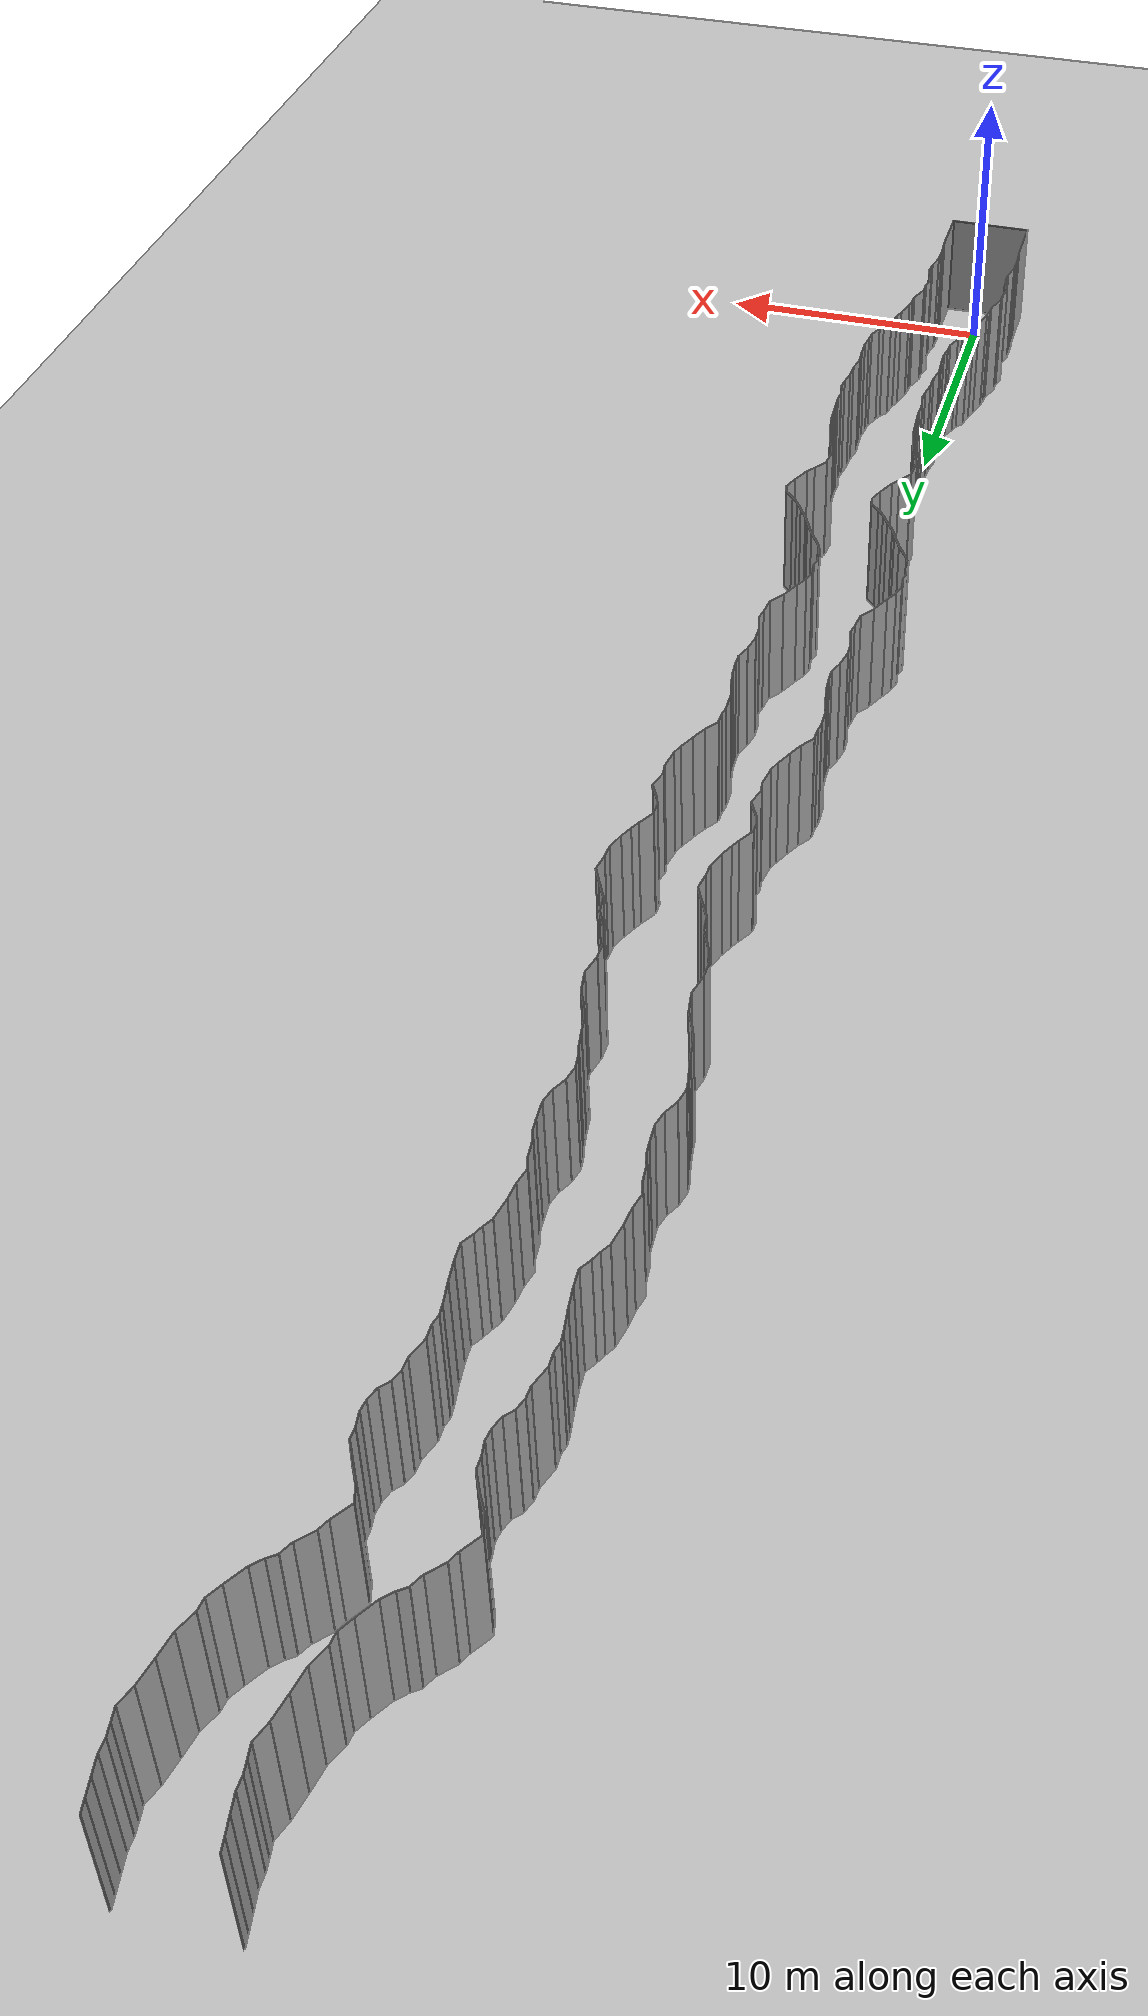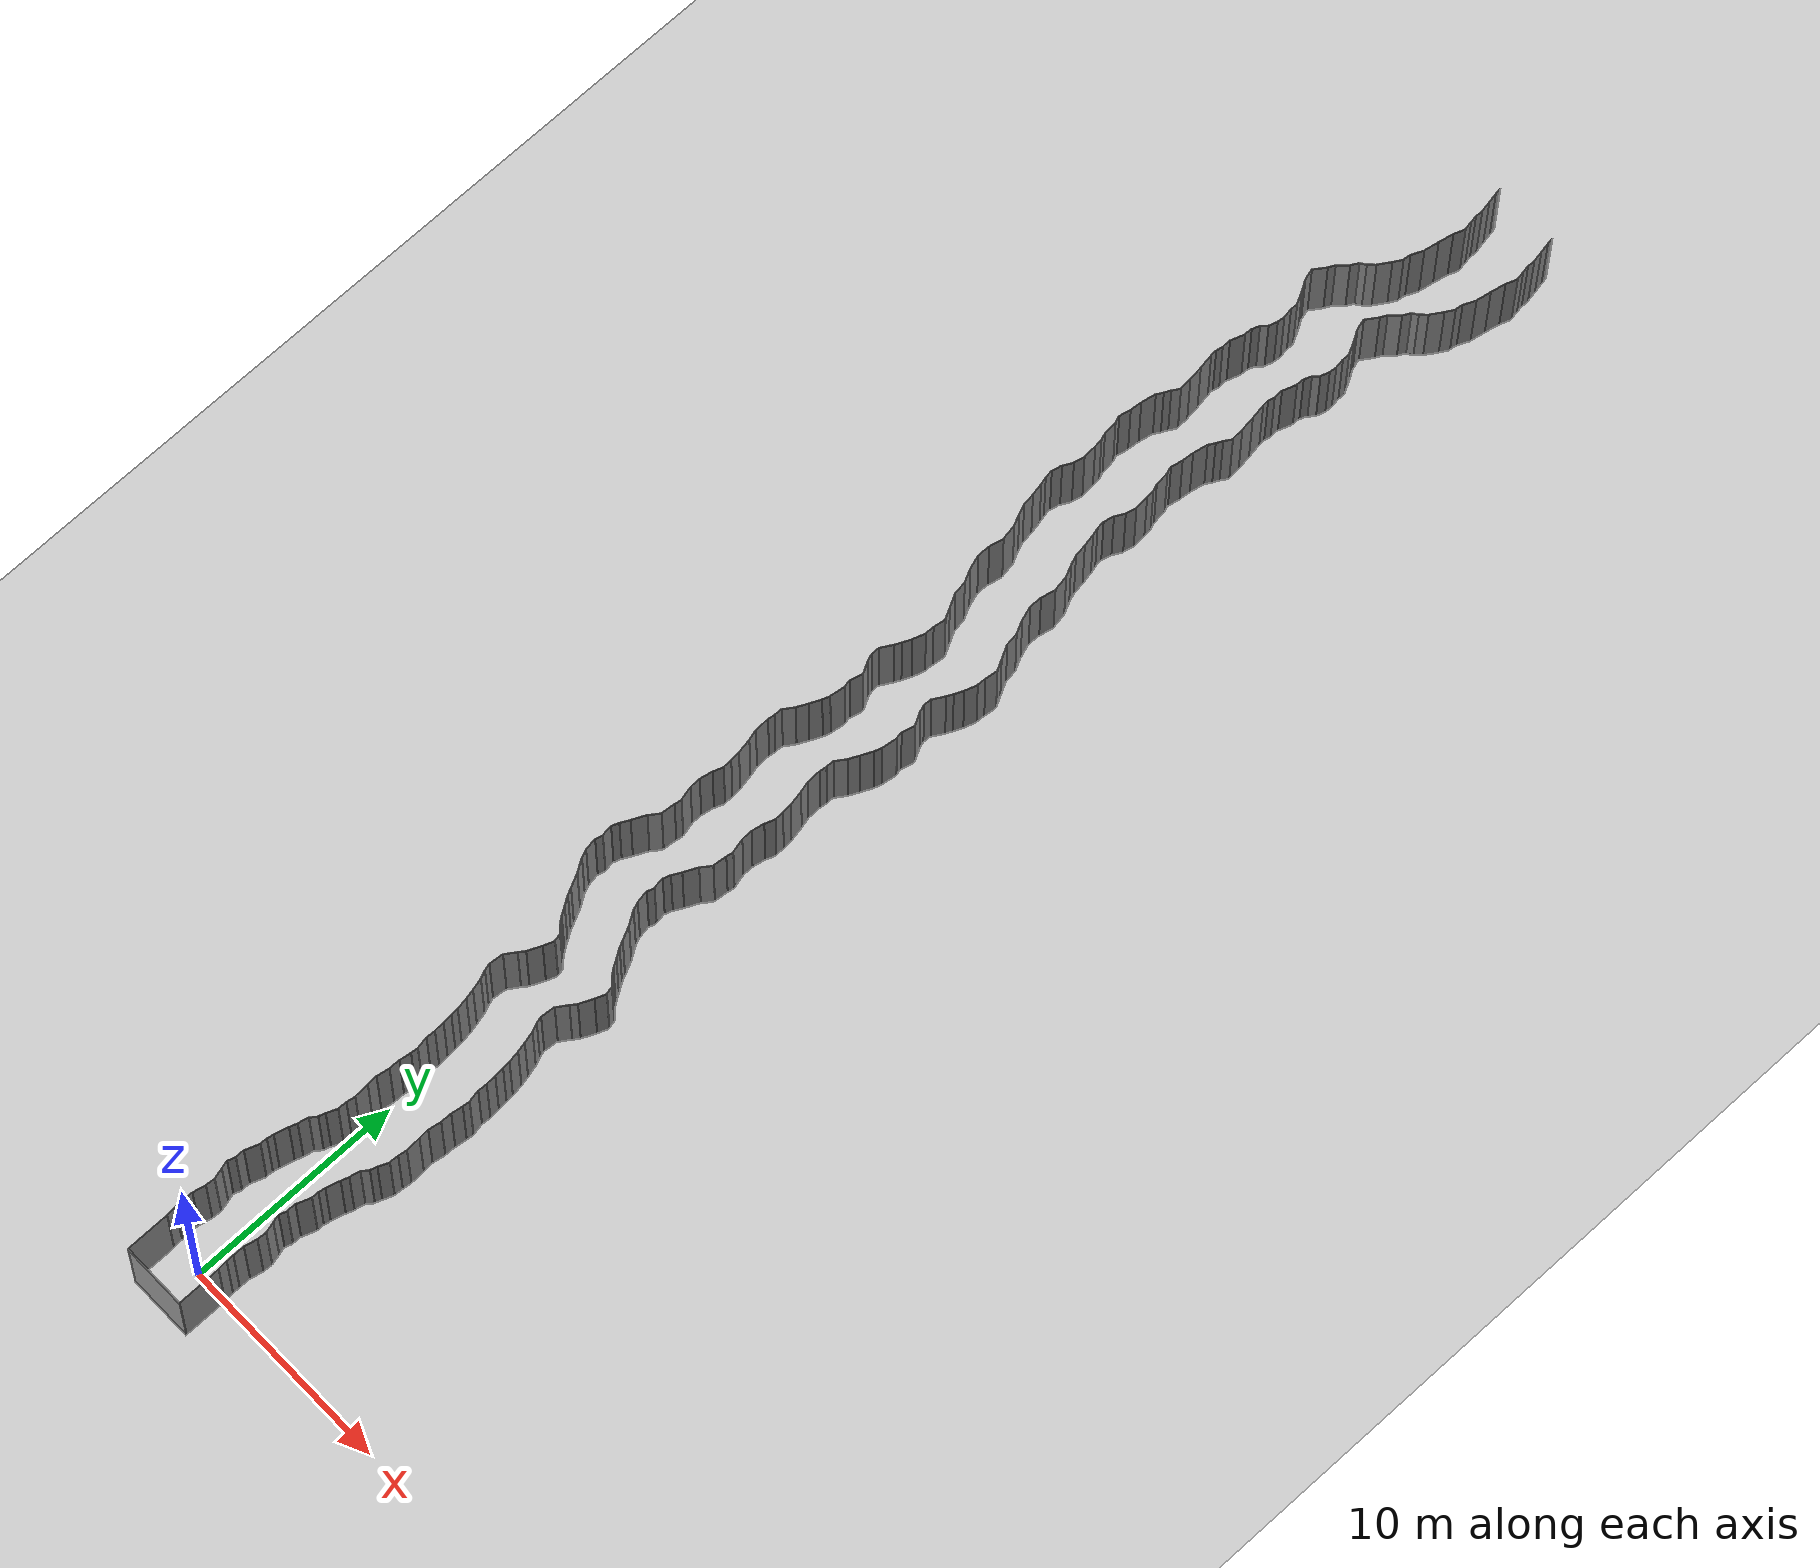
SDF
<sdf version="1.6">
 <world name="default">
  <light name="sun" type="directional">
   <pose>0 0 10 0 -0 0</pose>
   <diffuse>0.8 0.8 0.8 1</diffuse>
   <specular>0.2 0.2 0.2 1</specular>
   <attenuation>
    <range>1000</range>
    <constant>0.9</constant>
    <linear>0.01</linear>
    <quadratic>0.001</quadratic>
   </attenuation>
   <direction>-0.5 0.1 -0.9</direction>
  </light>
  <model name="ground_plane">
   <static>1</static>
   <link name="link">
    <collision name="collision">
     <geometry><plane><normal>0 0 1</normal><size>200 200</size></plane></geometry>
     <surface><friction><ode><mu>100</mu><mu2>50</mu2></ode></friction></surface>
    </collision>
    <visual name="visual">
     <cast_shadows>0</cast_shadows>
     <geometry><plane><normal>0 0 1</normal><size>200 200</size></plane></geometry>
     <material>
      <script><uri>file://media/materials/scripts/gazebo.material</uri><name>Gazebo/Grey</name></script>
     </material>
    </visual>
   </link>
   <pose>0 100 0 0 -0 0</pose>
  </model>
  <gravity>0 0 -9.8</gravity>
  <magnetic_field>6e-06 2.3e-05 -4.2e-05</magnetic_field>
  <atmosphere type="adiabatic"/>
  <physics default="0" name="default_physics" type="ode">
   <max_step_size>0.001</max_step_size>
   <real_time_factor>1</real_time_factor>
   <real_time_update_rate>1000</real_time_update_rate>
  </physics>
  <scene><ambient>0.4 0.4 0.4 1</ambient><background>0.7 0.7 0.7 1</background><shadows>1</shadows></scene>
  <spherical_coordinates>
   <surface_model>EARTH_WGS84</surface_model>
   <latitude_deg>0</latitude_deg>
   <longitude_deg>0</longitude_deg>
   <elevation>0</elevation>
   <heading_deg>0</heading_deg>
  </spherical_coordinates>
  <model name="wall_back">
   <static>1</static>
   <pose>0.0 -2 2 0.0 0 0.0</pose>
   <link name="link">
    <collision name="collision"><geometry><box><size>3 0.02 4</size></box></geometry></collision>
    <visual name="visual">
     <material>
      <script><name>Gazebo/Grey</name><uri>file://media/materials/scripts/gazebo.material</uri></script>
     </material>
     <geometry><box><size>3 0.02 4</size></box></geometry>
    </visual>
   </link>
  </model>
  <model name="wall_left">
   <static>1</static>
   <pose>1.5 -1 2 0 0 0.00</pose>
   <link name="link">
    <collision name="collision"><geometry><box><size>0.02 2 4</size></box></geometry></collision>
    <visual name="visual">
     <material>
      <script><name>Gazebo/Grey</name><uri>file://media/materials/scripts/gazebo.material</uri></script>
     </material>
     <geometry><box><size>0.02 2 4</size></box></geometry>
    </visual>
   </link>
  </model>
  <model name="wall_right">
   <static>1</static>
   <pose>-1.5 -1 2 0 0 0.00</pose>
   <link name="link">
    <collision name="collision"><geometry><box><size>0.02 2 4</size></box></geometry></collision>
    <visual name="visual">
     <material>
      <script><name>Gazebo/Grey</name><uri>file://media/materials/scripts/gazebo.material</uri></script>
     </material>
     <geometry><box><size>0.02 2 4</size></box></geometry>
    </visual>
   </link>
  </model>
  <model name="wall_0">
   <static>1</static>
   <pose>-1.517400405700846 0.22270519185213933 2 0 0 0.07797360765698158</pose>
   <link name="link">
    <collision name="collision"><geometry><box><size>0.02 0.446767843948 4</size></box></geometry></collision>
    <visual name="visual">
     <material>
      <script><name>Gazebo/Grey</name><uri>file://media/materials/scripts/gazebo.material</uri></script>
     </material>
     <geometry><box><size>0.02 0.446767843948 4</size></box></geometry>
    </visual>
   </link>
  </model>
  <model name="wall_1">
   <static>1</static>
   <pose>1.482599594299154 0.22270519185213933 2 0 0 0.07797360765698158</pose>
   <link name="link">
    <collision name="collision"><geometry><box><size>0.02 0.446767843948 4</size></box></geometry></collision>
    <visual name="visual">
     <material>
      <script><name>Gazebo/Grey</name><uri>file://media/materials/scripts/gazebo.material</uri></script>
     </material>
     <geometry><box><size>0.02 0.446767843948 4</size></box></geometry>
    </visual>
   </link>
  </model>
  <model name="wall_2">
   <static>1</static>
   <pose>-1.538484740069656 0.6191674311720261 2 0 0 0.021198431287549818</pose>
   <link name="link">
    <collision name="collision"><geometry><box><size>0.02 0.347592191369 4</size></box></geometry></collision>
    <visual name="visual">
     <material>
      <script><name>Gazebo/Grey</name><uri>file://media/materials/scripts/gazebo.material</uri></script>
     </material>
     <geometry><box><size>0.02 0.347592191369 4</size></box></geometry>
    </visual>
   </link>
  </model>
  <model name="wall_3">
   <static>1</static>
   <pose>1.461515259930344 0.6191674311720261 2 0 0 0.021198431287549818</pose>
   <link name="link">
    <collision name="collision"><geometry><box><size>0.02 0.347592191369 4</size></box></geometry></collision>
    <visual name="visual">
     <material>
      <script><name>Gazebo/Grey</name><uri>file://media/materials/scripts/gazebo.material</uri></script>
     </material>
     <geometry><box><size>0.02 0.347592191369 4</size></box></geometry>
    </visual>
   </link>
  </model>
  <model name="wall_4">
   <static>1</static>
   <pose>-1.5382475325272809 1.0614027822165968 2 0 0 -0.014604001111507356</pose>
   <link name="link">
    <collision name="collision"><geometry><box><size>0.02 0.537013872449 4</size></box></geometry></collision>
    <visual name="visual">
     <material>
      <script><name>Gazebo/Grey</name><uri>file://media/materials/scripts/gazebo.material</uri></script>
     </material>
     <geometry><box><size>0.02 0.537013872449 4</size></box></geometry>
    </visual>
   </link>
  </model>
  <model name="wall_5">
   <static>1</static>
   <pose>1.4617524674727191 1.0614027822165968 2 0 0 -0.014604001111507356</pose>
   <link name="link">
    <collision name="collision"><geometry><box><size>0.02 0.537013872449 4</size></box></geometry></collision>
    <visual name="visual">
     <material>
      <script><name>Gazebo/Grey</name><uri>file://media/materials/scripts/gazebo.material</uri></script>
     </material>
     <geometry><box><size>0.02 0.537013872449 4</size></box></geometry>
    </visual>
   </link>
  </model>
  <model name="wall_6">
   <static>1</static>
   <pose>-1.4690011064224104 1.6202511780744204 2 0 0 -0.22128828142202453</pose>
   <link name="link">
    <collision name="collision"><geometry><box><size>0.02 0.595255185584 4</size></box></geometry></collision>
    <visual name="visual">
     <material>
      <script><name>Gazebo/Grey</name><uri>file://media/materials/scripts/gazebo.material</uri></script>
     </material>
     <geometry><box><size>0.02 0.595255185584 4</size></box></geometry>
    </visual>
   </link>
  </model>
  <model name="wall_7">
   <static>1</static>
   <pose>1.5309988935775896 1.6202511780744204 2 0 0 -0.22128828142202453</pose>
   <link name="link">
    <collision name="collision"><geometry><box><size>0.02 0.595255185584 4</size></box></geometry></collision>
    <visual name="visual">
     <material>
      <script><name>Gazebo/Grey</name><uri>file://media/materials/scripts/gazebo.material</uri></script>
     </material>
     <geometry><box><size>0.02 0.595255185584 4</size></box></geometry>
    </visual>
   </link>
  </model>
  <model name="wall_8">
   <static>1</static>
   <pose>-1.3854139207875884 2.1224906012741633 2 0 0 -0.0859816332729206</pose>
   <link name="link">
    <collision name="collision"><geometry><box><size>0.02 0.425309817521 4</size></box></geometry></collision>
    <visual name="visual">
     <material>
      <script><name>Gazebo/Grey</name><uri>file://media/materials/scripts/gazebo.material</uri></script>
     </material>
     <geometry><box><size>0.02 0.425309817521 4</size></box></geometry>
    </visual>
   </link>
  </model>
  <model name="wall_9">
   <static>1</static>
   <pose>1.6145860792124116 2.1224906012741633 2 0 0 -0.0859816332729206</pose>
   <link name="link">
    <collision name="collision"><geometry><box><size>0.02 0.425309817521 4</size></box></geometry></collision>
    <visual name="visual">
     <material>
      <script><name>Gazebo/Grey</name><uri>file://media/materials/scripts/gazebo.material</uri></script>
     </material>
     <geometry><box><size>0.02 0.425309817521 4</size></box></geometry>
    </visual>
   </link>
  </model>
  <model name="wall_10">
   <static>1</static>
   <pose>-1.4278485293488319 2.5689880970863985 2 0 0 0.25314279067731127</pose>
   <link name="link">
    <collision name="collision"><geometry><box><size>0.02 0.484703791591 4</size></box></geometry></collision>
    <visual name="visual">
     <material>
      <script><name>Gazebo/Grey</name><uri>file://media/materials/scripts/gazebo.material</uri></script>
     </material>
     <geometry><box><size>0.02 0.484703791591 4</size></box></geometry>
    </visual>
   </link>
  </model>
  <model name="wall_11">
   <static>1</static>
   <pose>1.5721514706511681 2.5689880970863985 2 0 0 0.25314279067731127</pose>
   <link name="link">
    <collision name="collision"><geometry><box><size>0.02 0.484703791591 4</size></box></geometry></collision>
    <visual name="visual">
     <material>
      <script><name>Gazebo/Grey</name><uri>file://media/materials/scripts/gazebo.material</uri></script>
     </material>
     <geometry><box><size>0.02 0.484703791591 4</size></box></geometry>
    </visual>
   </link>
  </model>
  <model name="wall_12">
   <static>1</static>
   <pose>-1.5404899620019925 2.9866335350339854 2 0 0 0.2765523475475418</pose>
   <link name="link">
    <collision name="collision"><geometry><box><size>0.02 0.380492301197 4</size></box></geometry></collision>
    <visual name="visual">
     <material>
      <script><name>Gazebo/Grey</name><uri>file://media/materials/scripts/gazebo.material</uri></script>
     </material>
     <geometry><box><size>0.02 0.380492301197 4</size></box></geometry>
    </visual>
   </link>
  </model>
  <model name="wall_13">
   <static>1</static>
   <pose>1.4595100379980075 2.9866335350339854 2 0 0 0.2765523475475418</pose>
   <link name="link">
    <collision name="collision"><geometry><box><size>0.02 0.380492301197 4</size></box></geometry></collision>
    <visual name="visual">
     <material>
      <script><name>Gazebo/Grey</name><uri>file://media/materials/scripts/gazebo.material</uri></script>
     </material>
     <geometry><box><size>0.02 0.380492301197 4</size></box></geometry>
    </visual>
   </link>
  </model>
  <model name="wall_14">
   <static>1</static>
   <pose>-1.5325124790575746 3.343703439421072 2 0 0 -0.3315677890882658</pose>
   <link name="link">
    <collision name="collision"><geometry><box><size>0.02 0.368157650196 4</size></box></geometry></collision>
    <visual name="visual">
     <material>
      <script><name>Gazebo/Grey</name><uri>file://media/materials/scripts/gazebo.material</uri></script>
     </material>
     <geometry><box><size>0.02 0.368157650196 4</size></box></geometry>
    </visual>
   </link>
  </model>
  <model name="wall_15">
   <static>1</static>
   <pose>1.4674875209424254 3.343703439421072 2 0 0 -0.3315677890882658</pose>
   <link name="link">
    <collision name="collision"><geometry><box><size>0.02 0.368157650196 4</size></box></geometry></collision>
    <visual name="visual">
     <material>
      <script><name>Gazebo/Grey</name><uri>file://media/materials/scripts/gazebo.material</uri></script>
     </material>
     <geometry><box><size>0.02 0.368157650196 4</size></box></geometry>
    </visual>
   </link>
  </model>
  <model name="wall_16">
   <static>1</static>
   <pose>-1.4721097631918243 3.724370834767425 2 0 0 -0.002324633996140721</pose>
   <link name="link">
    <collision name="collision"><geometry><box><size>0.02 0.41323064456 4</size></box></geometry></collision>
    <visual name="visual">
     <material>
      <script><name>Gazebo/Grey</name><uri>file://media/materials/scripts/gazebo.material</uri></script>
     </material>
     <geometry><box><size>0.02 0.41323064456 4</size></box></geometry>
    </visual>
   </link>
  </model>
  <model name="wall_17">
   <static>1</static>
   <pose>1.5278902368081757 3.724370834767425 2 0 0 -0.002324633996140721</pose>
   <link name="link">
    <collision name="collision"><geometry><box><size>0.02 0.41323064456 4</size></box></geometry></collision>
    <visual name="visual">
     <material>
      <script><name>Gazebo/Grey</name><uri>file://media/materials/scripts/gazebo.material</uri></script>
     </material>
     <geometry><box><size>0.02 0.41323064456 4</size></box></geometry>
    </visual>
   </link>
  </model>
  <model name="wall_18">
   <static>1</static>
   <pose>-1.3517692520525595 4.256364432140748 2 0 0 -0.35294653380588364</pose>
   <link name="link">
    <collision name="collision"><geometry><box><size>0.02 0.693506609392 4</size></box></geometry></collision>
    <visual name="visual">
     <material>
      <script><name>Gazebo/Grey</name><uri>file://media/materials/scripts/gazebo.material</uri></script>
     </material>
     <geometry><box><size>0.02 0.693506609392 4</size></box></geometry>
    </visual>
   </link>
  </model>
  <model name="wall_19">
   <static>1</static>
   <pose>1.6482307479474405 4.256364432140748 2 0 0 -0.35294653380588364</pose>
   <link name="link">
    <collision name="collision"><geometry><box><size>0.02 0.693506609392 4</size></box></geometry></collision>
    <visual name="visual">
     <material>
      <script><name>Gazebo/Grey</name><uri>file://media/materials/scripts/gazebo.material</uri></script>
     </material>
     <geometry><box><size>0.02 0.693506609392 4</size></box></geometry>
    </visual>
   </link>
  </model>
  <model name="wall_20">
   <static>1</static>
   <pose>-1.227636711686697 4.744123964637654 2 0 0 -0.026304532438163615</pose>
   <link name="link">
    <collision name="collision"><geometry><box><size>0.02 0.324873786497 4</size></box></geometry></collision>
    <visual name="visual">
     <material>
      <script><name>Gazebo/Grey</name><uri>file://media/materials/scripts/gazebo.material</uri></script>
     </material>
     <geometry><box><size>0.02 0.324873786497 4</size></box></geometry>
    </visual>
   </link>
  </model>
  <model name="wall_21">
   <static>1</static>
   <pose>1.772363288313303 4.744123964637654 2 0 0 -0.026304532438163615</pose>
   <link name="link">
    <collision name="collision"><geometry><box><size>0.02 0.324873786497 4</size></box></geometry></collision>
    <visual name="visual">
     <material>
      <script><name>Gazebo/Grey</name><uri>file://media/materials/scripts/gazebo.material</uri></script>
     </material>
     <geometry><box><size>0.02 0.324873786497 4</size></box></geometry>
    </visual>
   </link>
  </model>
  <model name="wall_22">
   <static>1</static>
   <pose>-1.194815430475022 5.056967520714394 2 0 0 -0.1875117950377441</pose>
   <link name="link">
    <collision name="collision"><geometry><box><size>0.02 0.306294718969 4</size></box></geometry></collision>
    <visual name="visual">
     <material>
      <script><name>Gazebo/Grey</name><uri>file://media/materials/scripts/gazebo.material</uri></script>
     </material>
     <geometry><box><size>0.02 0.306294718969 4</size></box></geometry>
    </visual>
   </link>
  </model>
  <model name="wall_23">
   <static>1</static>
   <pose>1.805184569524978 5.056967520714394 2 0 0 -0.1875117950377441</pose>
   <link name="link">
    <collision name="collision"><geometry><box><size>0.02 0.306294718969 4</size></box></geometry></collision>
    <visual name="visual">
     <material>
      <script><name>Gazebo/Grey</name><uri>file://media/materials/scripts/gazebo.material</uri></script>
     </material>
     <geometry><box><size>0.02 0.306294718969 4</size></box></geometry>
    </visual>
   </link>
  </model>
  <model name="wall_24">
   <static>1</static>
   <pose>-1.079417371918186 5.526751582192476 2 0 0 -0.26555675770987125</pose>
   <link name="link">
    <collision name="collision"><geometry><box><size>0.02 0.6618422766 4</size></box></geometry></collision>
    <visual name="visual">
     <material>
      <script><name>Gazebo/Grey</name><uri>file://media/materials/scripts/gazebo.material</uri></script>
     </material>
     <geometry><box><size>0.02 0.6618422766 4</size></box></geometry>
    </visual>
   </link>
  </model>
  <model name="wall_25">
   <static>1</static>
   <pose>1.920582628081814 5.526751582192476 2 0 0 -0.26555675770987125</pose>
   <link name="link">
    <collision name="collision"><geometry><box><size>0.02 0.6618422766 4</size></box></geometry></collision>
    <visual name="visual">
     <material>
      <script><name>Gazebo/Grey</name><uri>file://media/materials/scripts/gazebo.material</uri></script>
     </material>
     <geometry><box><size>0.02 0.6618422766 4</size></box></geometry>
    </visual>
   </link>
  </model>
  <model name="wall_26">
   <static>1</static>
   <pose>-0.9331630423043914 6.019489471910388 2 0 0 -0.33002937253807935</pose>
   <link name="link">
    <collision name="collision"><geometry><box><size>0.02 0.366618748459 4</size></box></geometry></collision>
    <visual name="visual">
     <material>
      <script><name>Gazebo/Grey</name><uri>file://media/materials/scripts/gazebo.material</uri></script>
     </material>
     <geometry><box><size>0.02 0.366618748459 4</size></box></geometry>
    </visual>
   </link>
  </model>
  <model name="wall_27">
   <static>1</static>
   <pose>2.0668369576956085 6.019489471910388 2 0 0 -0.33002937253807935</pose>
   <link name="link">
    <collision name="collision"><geometry><box><size>0.02 0.366618748459 4</size></box></geometry></collision>
    <visual name="visual">
     <material>
      <script><name>Gazebo/Grey</name><uri>file://media/materials/scripts/gazebo.material</uri></script>
     </material>
     <geometry><box><size>0.02 0.366618748459 4</size></box></geometry>
    </visual>
   </link>
  </model>
  <model name="wall_28">
   <static>1</static>
   <pose>-0.8216548867542122 6.434227950047219 2 0 0 -0.21264242066373062</pose>
   <link name="link">
    <collision name="collision"><geometry><box><size>0.02 0.493764817735 4</size></box></geometry></collision>
    <visual name="visual">
     <material>
      <script><name>Gazebo/Grey</name><uri>file://media/materials/scripts/gazebo.material</uri></script>
     </material>
     <geometry><box><size>0.02 0.493764817735 4</size></box></geometry>
    </visual>
   </link>
  </model>
  <model name="wall_29">
   <static>1</static>
   <pose>2.178345113245788 6.434227950047219 2 0 0 -0.21264242066373062</pose>
   <link name="link">
    <collision name="collision"><geometry><box><size>0.02 0.493764817735 4</size></box></geometry></collision>
    <visual name="visual">
     <material>
      <script><name>Gazebo/Grey</name><uri>file://media/materials/scripts/gazebo.material</uri></script>
     </material>
     <geometry><box><size>0.02 0.493764817735 4</size></box></geometry>
    </visual>
   </link>
  </model>
  <model name="wall_30">
   <static>1</static>
   <pose>-0.6594195212636004 6.822402548026057 2 0 0 -0.6434698371133363</pose>
   <link name="link">
    <collision name="collision"><geometry><box><size>0.02 0.367123402309 4</size></box></geometry></collision>
    <visual name="visual">
     <material>
      <script><name>Gazebo/Grey</name><uri>file://media/materials/scripts/gazebo.material</uri></script>
     </material>
     <geometry><box><size>0.02 0.367123402309 4</size></box></geometry>
    </visual>
   </link>
  </model>
  <model name="wall_31">
   <static>1</static>
   <pose>2.3405804787363995 6.822402548026057 2 0 0 -0.6434698371133363</pose>
   <link name="link">
    <collision name="collision"><geometry><box><size>0.02 0.367123402309 4</size></box></geometry></collision>
    <visual name="visual">
     <material>
      <script><name>Gazebo/Grey</name><uri>file://media/materials/scripts/gazebo.material</uri></script>
     </material>
     <geometry><box><size>0.02 0.367123402309 4</size></box></geometry>
    </visual>
   </link>
  </model>
  <model name="wall_32">
   <static>1</static>
   <pose>-0.5002769118110462 7.120379788905422 2 0 0 -0.3136017950999182</pose>
   <link name="link">
    <collision name="collision"><geometry><box><size>0.02 0.317745766039 4</size></box></geometry></collision>
    <visual name="visual">
     <material>
      <script><name>Gazebo/Grey</name><uri>file://media/materials/scripts/gazebo.material</uri></script>
     </material>
     <geometry><box><size>0.02 0.317745766039 4</size></box></geometry>
    </visual>
   </link>
  </model>
  <model name="wall_33">
   <static>1</static>
   <pose>2.499723088188954 7.120379788905422 2 0 0 -0.3136017950999182</pose>
   <link name="link">
    <collision name="collision"><geometry><box><size>0.02 0.317745766039 4</size></box></geometry></collision>
    <visual name="visual">
     <material>
      <script><name>Gazebo/Grey</name><uri>file://media/materials/scripts/gazebo.material</uri></script>
     </material>
     <geometry><box><size>0.02 0.317745766039 4</size></box></geometry>
    </visual>
   </link>
  </model>
  <model name="wall_34">
   <static>1</static>
   <pose>-0.3526167482036617 7.508015287731277 2 0 0 -0.39516468108146524</pose>
   <link name="link">
    <collision name="collision"><geometry><box><size>0.02 0.512520446292 4</size></box></geometry></collision>
    <visual name="visual">
     <material>
      <script><name>Gazebo/Grey</name><uri>file://media/materials/scripts/gazebo.material</uri></script>
     </material>
     <geometry><box><size>0.02 0.512520446292 4</size></box></geometry>
    </visual>
   </link>
  </model>
  <model name="wall_35">
   <static>1</static>
   <pose>2.6473832517963385 7.508015287731277 2 0 0 -0.39516468108146524</pose>
   <link name="link">
    <collision name="collision"><geometry><box><size>0.02 0.512520446292 4</size></box></geometry></collision>
    <visual name="visual">
     <material>
      <script><name>Gazebo/Grey</name><uri>file://media/materials/scripts/gazebo.material</uri></script>
     </material>
     <geometry><box><size>0.02 0.512520446292 4</size></box></geometry>
    </visual>
   </link>
  </model>
  <model name="wall_36">
   <static>1</static>
   <pose>-0.24348783561851456 7.948004685225667 2 0 0 -0.05145354108220038</pose>
   <link name="link">
    <collision name="collision"><geometry><box><size>0.02 0.407495966095 4</size></box></geometry></collision>
    <visual name="visual">
     <material>
      <script><name>Gazebo/Grey</name><uri>file://media/materials/scripts/gazebo.material</uri></script>
     </material>
     <geometry><box><size>0.02 0.407495966095 4</size></box></geometry>
    </visual>
   </link>
  </model>
  <model name="wall_37">
   <static>1</static>
   <pose>2.7565121643814856 7.948004685225667 2 0 0 -0.05145354108220038</pose>
   <link name="link">
    <collision name="collision"><geometry><box><size>0.02 0.407495966095 4</size></box></geometry></collision>
    <visual name="visual">
     <material>
      <script><name>Gazebo/Grey</name><uri>file://media/materials/scripts/gazebo.material</uri></script>
     </material>
     <geometry><box><size>0.02 0.407495966095 4</size></box></geometry>
    </visual>
   </link>
  </model>
  <model name="wall_38">
   <static>1</static>
   <pose>-0.20231427958396506 8.353806132833219 2 0 0 -0.15056279947688372</pose>
   <link name="link">
    <collision name="collision"><geometry><box><size>0.02 0.409276445221 4</size></box></geometry></collision>
    <visual name="visual">
     <material>
      <script><name>Gazebo/Grey</name><uri>file://media/materials/scripts/gazebo.material</uri></script>
     </material>
     <geometry><box><size>0.02 0.409276445221 4</size></box></geometry>
    </visual>
   </link>
  </model>
  <model name="wall_39">
   <static>1</static>
   <pose>2.797685720416035 8.353806132833219 2 0 0 -0.15056279947688372</pose>
   <link name="link">
    <collision name="collision"><geometry><box><size>0.02 0.409276445221 4</size></box></geometry></collision>
    <visual name="visual">
     <material>
      <script><name>Gazebo/Grey</name><uri>file://media/materials/scripts/gazebo.material</uri></script>
     </material>
     <geometry><box><size>0.02 0.409276445221 4</size></box></geometry>
    </visual>
   </link>
  </model>
  <model name="wall_40">
   <static>1</static>
   <pose>-0.18269914202459525 8.892090272240686 2 0 0 0.03296654550663393</pose>
   <link name="link">
    <collision name="collision"><geometry><box><size>0.02 0.672287338196 4</size></box></geometry></collision>
    <visual name="visual">
     <material>
      <script><name>Gazebo/Grey</name><uri>file://media/materials/scripts/gazebo.material</uri></script>
     </material>
     <geometry><box><size>0.02 0.672287338196 4</size></box></geometry>
    </visual>
   </link>
  </model>
  <model name="wall_41">
   <static>1</static>
   <pose>2.817300857975405 8.892090272240686 2 0 0 0.03296654550663393</pose>
   <link name="link">
    <collision name="collision"><geometry><box><size>0.02 0.672287338196 4</size></box></geometry></collision>
    <visual name="visual">
     <material>
      <script><name>Gazebo/Grey</name><uri>file://media/materials/scripts/gazebo.material</uri></script>
     </material>
     <geometry><box><size>0.02 0.672287338196 4</size></box></geometry>
    </visual>
   </link>
  </model>
  <model name="wall_42">
   <static>1</static>
   <pose>-0.21465609067422717 9.474038734755839 2 0 0 0.0846691498733114</pose>
   <link name="link">
    <collision name="collision"><geometry><box><size>0.02 0.493743605961 4</size></box></geometry></collision>
    <visual name="visual">
     <material>
      <script><name>Gazebo/Grey</name><uri>file://media/materials/scripts/gazebo.material</uri></script>
     </material>
     <geometry><box><size>0.02 0.493743605961 4</size></box></geometry>
    </visual>
   </link>
  </model>
  <model name="wall_43">
   <static>1</static>
   <pose>2.785343909325773 9.474038734755839 2 0 0 0.0846691498733114</pose>
   <link name="link">
    <collision name="collision"><geometry><box><size>0.02 0.493743605961 4</size></box></geometry></collision>
    <visual name="visual">
     <material>
      <script><name>Gazebo/Grey</name><uri>file://media/materials/scripts/gazebo.material</uri></script>
     </material>
     <geometry><box><size>0.02 0.493743605961 4</size></box></geometry>
    </visual>
   </link>
  </model>
  <model name="wall_44">
   <static>1</static>
   <pose>-0.1829470090662563 10.011152340408753 2 0 0 -0.17870450283797976</pose>
   <link name="link">
    <collision name="collision"><geometry><box><size>0.02 0.591674880066 4</size></box></geometry></collision>
    <visual name="visual">
     <material>
      <script><name>Gazebo/Grey</name><uri>file://media/materials/scripts/gazebo.material</uri></script>
     </material>
     <geometry><box><size>0.02 0.591674880066 4</size></box></geometry>
    </visual>
   </link>
  </model>
  <model name="wall_45">
   <static>1</static>
   <pose>2.817052990933744 10.011152340408753 2 0 0 -0.17870450283797976</pose>
   <link name="link">
    <collision name="collision"><geometry><box><size>0.02 0.591674880066 4</size></box></geometry></collision>
    <visual name="visual">
     <material>
      <script><name>Gazebo/Grey</name><uri>file://media/materials/scripts/gazebo.material</uri></script>
     </material>
     <geometry><box><size>0.02 0.591674880066 4</size></box></geometry>
    </visual>
   </link>
  </model>
  <model name="wall_46">
   <static>1</static>
   <pose>-0.12374734299135838 10.556126179677776 2 0 0 -0.026045654928100116</pose>
   <link name="link">
    <collision name="collision"><geometry><box><size>0.02 0.507867592501 4</size></box></geometry></collision>
    <visual name="visual">
     <material>
      <script><name>Gazebo/Grey</name><uri>file://media/materials/scripts/gazebo.material</uri></script>
     </material>
     <geometry><box><size>0.02 0.507867592501 4</size></box></geometry>
    </visual>
   </link>
  </model>
  <model name="wall_47">
   <static>1</static>
   <pose>2.8762526570086417 10.556126179677776 2 0 0 -0.026045654928100116</pose>
   <link name="link">
    <collision name="collision"><geometry><box><size>0.02 0.507867592501 4</size></box></geometry></collision>
    <visual name="visual">
     <material>
      <script><name>Gazebo/Grey</name><uri>file://media/materials/scripts/gazebo.material</uri></script>
     </material>
     <geometry><box><size>0.02 0.507867592501 4</size></box></geometry>
    </visual>
   </link>
  </model>
  <model name="wall_48">
   <static>1</static>
   <pose>-0.07644699972790331 11.076148313374654 2 0 0 -0.15168506396018802</pose>
   <link name="link">
    <collision name="collision"><geometry><box><size>0.02 0.53853243177 4</size></box></geometry></collision>
    <visual name="visual">
     <material>
      <script><name>Gazebo/Grey</name><uri>file://media/materials/scripts/gazebo.material</uri></script>
     </material>
     <geometry><box><size>0.02 0.53853243177 4</size></box></geometry>
    </visual>
   </link>
  </model>
  <model name="wall_49">
   <static>1</static>
   <pose>2.9235530002720966 11.076148313374654 2 0 0 -0.15168506396018802</pose>
   <link name="link">
    <collision name="collision"><geometry><box><size>0.02 0.53853243177 4</size></box></geometry></collision>
    <visual name="visual">
     <material>
      <script><name>Gazebo/Grey</name><uri>file://media/materials/scripts/gazebo.material</uri></script>
     </material>
     <geometry><box><size>0.02 0.53853243177 4</size></box></geometry>
    </visual>
   </link>
  </model>
  <model name="wall_50">
   <static>1</static>
   <pose>-0.01497469235773137 11.502896802387374 2 0 0 -0.12872663914691143</pose>
   <link name="link">
    <collision name="collision"><geometry><box><size>0.02 0.323827345618 4</size></box></geometry></collision>
    <visual name="visual">
     <material>
      <script><name>Gazebo/Grey</name><uri>file://media/materials/scripts/gazebo.material</uri></script>
     </material>
     <geometry><box><size>0.02 0.323827345618 4</size></box></geometry>
    </visual>
   </link>
  </model>
  <model name="wall_51">
   <static>1</static>
   <pose>2.985025307642269 11.502896802387374 2 0 0 -0.12872663914691143</pose>
   <link name="link">
    <collision name="collision"><geometry><box><size>0.02 0.323827345618 4</size></box></geometry></collision>
    <visual name="visual">
     <material>
      <script><name>Gazebo/Grey</name><uri>file://media/materials/scripts/gazebo.material</uri></script>
     </material>
     <geometry><box><size>0.02 0.323827345618 4</size></box></geometry>
    </visual>
   </link>
  </model>
  <model name="wall_52">
   <static>1</static>
   <pose>-0.04615767591568272 11.933152148315687 2 0 0 0.19036829829793145</pose>
   <link name="link">
    <collision name="collision"><geometry><box><size>0.02 0.549285700864 4</size></box></geometry></collision>
    <visual name="visual">
     <material>
      <script><name>Gazebo/Grey</name><uri>file://media/materials/scripts/gazebo.material</uri></script>
     </material>
     <geometry><box><size>0.02 0.549285700864 4</size></box></geometry>
    </visual>
   </link>
  </model>
  <model name="wall_53">
   <static>1</static>
   <pose>2.9538423240843175 11.933152148315687 2 0 0 0.19036829829793145</pose>
   <link name="link">
    <collision name="collision"><geometry><box><size>0.02 0.549285700864 4</size></box></geometry></collision>
    <visual name="visual">
     <material>
      <script><name>Gazebo/Grey</name><uri>file://media/materials/scripts/gazebo.material</uri></script>
     </material>
     <geometry><box><size>0.02 0.549285700864 4</size></box></geometry>
    </visual>
   </link>
  </model>
  <model name="wall_54">
   <static>1</static>
   <pose>-0.08553015207405498 12.414556490212302 2 0 0 -0.059420878645683</pose>
   <link name="link">
    <collision name="collision"><geometry><box><size>0.02 0.424194703844 4</size></box></geometry></collision>
    <visual name="visual">
     <material>
      <script><name>Gazebo/Grey</name><uri>file://media/materials/scripts/gazebo.material</uri></script>
     </material>
     <geometry><box><size>0.02 0.424194703844 4</size></box></geometry>
    </visual>
   </link>
  </model>
  <model name="wall_55">
   <static>1</static>
   <pose>2.914469847925945 12.414556490212302 2 0 0 -0.059420878645683</pose>
   <link name="link">
    <collision name="collision"><geometry><box><size>0.02 0.424194703844 4</size></box></geometry></collision>
    <visual name="visual">
     <material>
      <script><name>Gazebo/Grey</name><uri>file://media/materials/scripts/gazebo.material</uri></script>
     </material>
     <geometry><box><size>0.02 0.424194703844 4</size></box></geometry>
    </visual>
   </link>
  </model>
  <model name="wall_56">
   <static>1</static>
   <pose>-0.08622264358435099 12.861903929554948 2 0 0 0.05633553169933642</pose>
   <link name="link">
    <collision name="collision"><geometry><box><size>0.02 0.471997626016 4</size></box></geometry></collision>
    <visual name="visual">
     <material>
      <script><name>Gazebo/Grey</name><uri>file://media/materials/scripts/gazebo.material</uri></script>
     </material>
     <geometry><box><size>0.02 0.471997626016 4</size></box></geometry>
    </visual>
   </link>
  </model>
  <model name="wall_57">
   <static>1</static>
   <pose>2.913777356415649 12.861903929554948 2 0 0 0.05633553169933642</pose>
   <link name="link">
    <collision name="collision"><geometry><box><size>0.02 0.471997626016 4</size></box></geometry></collision>
    <visual name="visual">
     <material>
      <script><name>Gazebo/Grey</name><uri>file://media/materials/scripts/gazebo.material</uri></script>
     </material>
     <geometry><box><size>0.02 0.471997626016 4</size></box></geometry>
    </visual>
   </link>
  </model>
  <model name="wall_58">
   <static>1</static>
   <pose>-0.1146179216074153 13.314674111700484 2 0 0 0.06945973517018125</pose>
   <link name="link">
    <collision name="collision"><geometry><box><size>0.02 0.435341291348 4</size></box></geometry></collision>
    <visual name="visual">
     <material>
      <script><name>Gazebo/Grey</name><uri>file://media/materials/scripts/gazebo.material</uri></script>
     </material>
     <geometry><box><size>0.02 0.435341291348 4</size></box></geometry>
    </visual>
   </link>
  </model>
  <model name="wall_59">
   <static>1</static>
   <pose>2.8853820783925848 13.314674111700484 2 0 0 0.06945973517018125</pose>
   <link name="link">
    <collision name="collision"><geometry><box><size>0.02 0.435341291348 4</size></box></geometry></collision>
    <visual name="visual">
     <material>
      <script><name>Gazebo/Grey</name><uri>file://media/materials/scripts/gazebo.material</uri></script>
     </material>
     <geometry><box><size>0.02 0.435341291348 4</size></box></geometry>
    </visual>
   </link>
  </model>
  <model name="wall_60">
   <static>1</static>
   <pose>-0.13839154024767428 13.708374575658198 2 0 0 0.049046994777524645</pose>
   <link name="link">
    <collision name="collision"><geometry><box><size>0.02 0.353534547607 4</size></box></geometry></collision>
    <visual name="visual">
     <material>
      <script><name>Gazebo/Grey</name><uri>file://media/materials/scripts/gazebo.material</uri></script>
     </material>
     <geometry><box><size>0.02 0.353534547607 4</size></box></geometry>
    </visual>
   </link>
  </model>
  <model name="wall_61">
   <static>1</static>
   <pose>2.861608459752326 13.708374575658198 2 0 0 0.049046994777524645</pose>
   <link name="link">
    <collision name="collision"><geometry><box><size>0.02 0.353534547607 4</size></box></geometry></collision>
    <visual name="visual">
     <material>
      <script><name>Gazebo/Grey</name><uri>file://media/materials/scripts/gazebo.material</uri></script>
     </material>
     <geometry><box><size>0.02 0.353534547607 4</size></box></geometry>
    </visual>
   </link>
  </model>
  <model name="wall_62">
   <static>1</static>
   <pose>-0.18932486366315185 14.148777225991369 2 0 0 0.15884455060752128</pose>
   <link name="link">
    <collision name="collision"><geometry><box><size>0.02 0.534423919061 4</size></box></geometry></collision>
    <visual name="visual">
     <material>
      <script><name>Gazebo/Grey</name><uri>file://media/materials/scripts/gazebo.material</uri></script>
     </material>
     <geometry><box><size>0.02 0.534423919061 4</size></box></geometry>
    </visual>
   </link>
  </model>
  <model name="wall_63">
   <static>1</static>
   <pose>2.8106751363368483 14.148777225991369 2 0 0 0.15884455060752128</pose>
   <link name="link">
    <collision name="collision"><geometry><box><size>0.02 0.534423919061 4</size></box></geometry></collision>
    <visual name="visual">
     <material>
      <script><name>Gazebo/Grey</name><uri>file://media/materials/scripts/gazebo.material</uri></script>
     </material>
     <geometry><box><size>0.02 0.534423919061 4</size></box></geometry>
    </visual>
   </link>
  </model>
  <model name="wall_64">
   <static>1</static>
   <pose>-0.2785587440005248 14.629385538147812 2 0 0 0.2133785116715421</pose>
   <link name="link">
    <collision name="collision"><geometry><box><size>0.02 0.443580667524 4</size></box></geometry></collision>
    <visual name="visual">
     <material>
      <script><name>Gazebo/Grey</name><uri>file://media/materials/scripts/gazebo.material</uri></script>
     </material>
     <geometry><box><size>0.02 0.443580667524 4</size></box></geometry>
    </visual>
   </link>
  </model>
  <model name="wall_65">
   <static>1</static>
   <pose>2.7214412559994754 14.629385538147812 2 0 0 0.2133785116715421</pose>
   <link name="link">
    <collision name="collision"><geometry><box><size>0.02 0.443580667524 4</size></box></geometry></collision>
    <visual name="visual">
     <material>
      <script><name>Gazebo/Grey</name><uri>file://media/materials/scripts/gazebo.material</uri></script>
     </material>
     <geometry><box><size>0.02 0.443580667524 4</size></box></geometry>
    </visual>
   </link>
  </model>
  <model name="wall_66">
   <static>1</static>
   <pose>-0.390800484489883 15.110812577996494 2 0 0 0.2418044379152058</pose>
   <link name="link">
    <collision name="collision"><geometry><box><size>0.02 0.545194439255 4</size></box></geometry></collision>
    <visual name="visual">
     <material>
      <script><name>Gazebo/Grey</name><uri>file://media/materials/scripts/gazebo.material</uri></script>
     </material>
     <geometry><box><size>0.02 0.545194439255 4</size></box></geometry>
    </visual>
   </link>
  </model>
  <model name="wall_67">
   <static>1</static>
   <pose>2.609199515510117 15.110812577996494 2 0 0 0.2418044379152058</pose>
   <link name="link">
    <collision name="collision"><geometry><box><size>0.02 0.545194439255 4</size></box></geometry></collision>
    <visual name="visual">
     <material>
      <script><name>Gazebo/Grey</name><uri>file://media/materials/scripts/gazebo.material</uri></script>
     </material>
     <geometry><box><size>0.02 0.545194439255 4</size></box></geometry>
    </visual>
   </link>
  </model>
  <model name="wall_68">
   <static>1</static>
   <pose>-0.5311126606760186 15.551350264213484 2 0 0 0.40327726630793564</pose>
   <link name="link">
    <collision name="collision"><geometry><box><size>0.02 0.382419800872 4</size></box></geometry></collision>
    <visual name="visual">
     <material>
      <script><name>Gazebo/Grey</name><uri>file://media/materials/scripts/gazebo.material</uri></script>
     </material>
     <geometry><box><size>0.02 0.382419800872 4</size></box></geometry>
    </visual>
   </link>
  </model>
  <model name="wall_69">
   <static>1</static>
   <pose>2.4688873393239814 15.551350264213484 2 0 0 0.40327726630793564</pose>
   <link name="link">
    <collision name="collision"><geometry><box><size>0.02 0.382419800872 4</size></box></geometry></collision>
    <visual name="visual">
     <material>
      <script><name>Gazebo/Grey</name><uri>file://media/materials/scripts/gazebo.material</uri></script>
     </material>
     <geometry><box><size>0.02 0.382419800872 4</size></box></geometry>
    </visual>
   </link>
  </model>
  <model name="wall_70">
   <static>1</static>
   <pose>-0.650011105229502 15.883077553922028 2 0 0 0.27432468117290343</pose>
   <link name="link">
    <collision name="collision"><geometry><box><size>0.02 0.323820752247 4</size></box></geometry></collision>
    <visual name="visual">
     <material>
      <script><name>Gazebo/Grey</name><uri>file://media/materials/scripts/gazebo.material</uri></script>
     </material>
     <geometry><box><size>0.02 0.323820752247 4</size></box></geometry>
    </visual>
   </link>
  </model>
  <model name="wall_71">
   <static>1</static>
   <pose>2.349988894770498 15.883077553922028 2 0 0 0.27432468117290343</pose>
   <link name="link">
    <collision name="collision"><geometry><box><size>0.02 0.323820752247 4</size></box></geometry></collision>
    <visual name="visual">
     <material>
      <script><name>Gazebo/Grey</name><uri>file://media/materials/scripts/gazebo.material</uri></script>
     </material>
     <geometry><box><size>0.02 0.323820752247 4</size></box></geometry>
    </visual>
   </link>
  </model>
  <model name="wall_72">
   <static>1</static>
   <pose>-0.6640294373326504 16.37140859971622 2 0 0 -0.089519372657797</pose>
   <link name="link">
    <collision name="collision"><geometry><box><size>0.02 0.667622813229 4</size></box></geometry></collision>
    <visual name="visual">
     <material>
      <script><name>Gazebo/Grey</name><uri>file://media/materials/scripts/gazebo.material</uri></script>
     </material>
     <geometry><box><size>0.02 0.667622813229 4</size></box></geometry>
    </visual>
   </link>
  </model>
  <model name="wall_73">
   <static>1</static>
   <pose>2.3359705626673497 16.37140859971622 2 0 0 -0.089519372657797</pose>
   <link name="link">
    <collision name="collision"><geometry><box><size>0.02 0.667622813229 4</size></box></geometry></collision>
    <visual name="visual">
     <material>
      <script><name>Gazebo/Grey</name><uri>file://media/materials/scripts/gazebo.material</uri></script>
     </material>
     <geometry><box><size>0.02 0.667622813229 4</size></box></geometry>
    </visual>
   </link>
  </model>
  <model name="wall_74">
   <static>1</static>
   <pose>-0.4746622099451455 16.946811892796788 2 0 0 -0.5810517609372926</pose>
   <link name="link">
    <collision name="collision"><geometry><box><size>0.02 0.581248131145 4</size></box></geometry></collision>
    <visual name="visual">
     <material>
      <script><name>Gazebo/Grey</name><uri>file://media/materials/scripts/gazebo.material</uri></script>
     </material>
     <geometry><box><size>0.02 0.581248131145 4</size></box></geometry>
    </visual>
   </link>
  </model>
  <model name="wall_75">
   <static>1</static>
   <pose>2.5253377900548544 16.946811892796788 2 0 0 -0.5810517609372926</pose>
   <link name="link">
    <collision name="collision"><geometry><box><size>0.02 0.581248131145 4</size></box></geometry></collision>
    <visual name="visual">
     <material>
      <script><name>Gazebo/Grey</name><uri>file://media/materials/scripts/gazebo.material</uri></script>
     </material>
     <geometry><box><size>0.02 0.581248131145 4</size></box></geometry>
    </visual>
   </link>
  </model>
  <model name="wall_76">
   <static>1</static>
   <pose>-0.21723060006269176 17.325044556159224 2 0 0 -0.6263947883843448</pose>
   <link name="link">
    <collision name="collision"><geometry><box><size>0.02 0.334023975592 4</size></box></geometry></collision>
    <visual name="visual">
     <material>
      <script><name>Gazebo/Grey</name><uri>file://media/materials/scripts/gazebo.material</uri></script>
     </material>
     <geometry><box><size>0.02 0.334023975592 4</size></box></geometry>
    </visual>
   </link>
  </model>
  <model name="wall_77">
   <static>1</static>
   <pose>2.782769399937308 17.325044556159224 2 0 0 -0.6263947883843448</pose>
   <link name="link">
    <collision name="collision"><geometry><box><size>0.02 0.334023975592 4</size></box></geometry></collision>
    <visual name="visual">
     <material>
      <script><name>Gazebo/Grey</name><uri>file://media/materials/scripts/gazebo.material</uri></script>
     </material>
     <geometry><box><size>0.02 0.334023975592 4</size></box></geometry>
    </visual>
   </link>
  </model>
  <model name="wall_78">
   <static>1</static>
   <pose>0.02140972928436677 17.767383102350284 2 0 0 -0.42978690551108095</pose>
   <link name="link">
    <collision name="collision"><geometry><box><size>0.02 0.675502713329 4</size></box></geometry></collision>
    <visual name="visual">
     <material>
      <script><name>Gazebo/Grey</name><uri>file://media/materials/scripts/gazebo.material</uri></script>
     </material>
     <geometry><box><size>0.02 0.675502713329 4</size></box></geometry>
    </visual>
   </link>
  </model>
  <model name="wall_79">
   <static>1</static>
   <pose>3.021409729284367 17.767383102350284 2 0 0 -0.42978690551108095</pose>
   <link name="link">
    <collision name="collision"><geometry><box><size>0.02 0.675502713329 4</size></box></geometry></collision>
    <visual name="visual">
     <material>
      <script><name>Gazebo/Grey</name><uri>file://media/materials/scripts/gazebo.material</uri></script>
     </material>
     <geometry><box><size>0.02 0.675502713329 4</size></box></geometry>
    </visual>
   </link>
  </model>
  <model name="wall_80">
   <static>1</static>
   <pose>0.2540347208641519 18.3155219190294 2 0 0 -0.3641326609913609</pose>
   <link name="link">
    <collision name="collision"><geometry><box><size>0.02 0.51604428271 4</size></box></geometry></collision>
    <visual name="visual">
     <material>
      <script><name>Gazebo/Grey</name><uri>file://media/materials/scripts/gazebo.material</uri></script>
     </material>
     <geometry><box><size>0.02 0.51604428271 4</size></box></geometry>
    </visual>
   </link>
  </model>
  <model name="wall_81">
   <static>1</static>
   <pose>3.254034720864152 18.3155219190294 2 0 0 -0.3641326609913609</pose>
   <link name="link">
    <collision name="collision"><geometry><box><size>0.02 0.51604428271 4</size></box></geometry></collision>
    <visual name="visual">
     <material>
      <script><name>Gazebo/Grey</name><uri>file://media/materials/scripts/gazebo.material</uri></script>
     </material>
     <geometry><box><size>0.02 0.51604428271 4</size></box></geometry>
    </visual>
   </link>
  </model>
  <model name="wall_82">
   <static>1</static>
   <pose>0.3101433915641246 18.72050041218852 2 0 0 0.21498268400877432</pose>
   <link name="link">
    <collision name="collision"><geometry><box><size>0.02 0.335470681532 4</size></box></geometry></collision>
    <visual name="visual">
     <material>
      <script><name>Gazebo/Grey</name><uri>file://media/materials/scripts/gazebo.material</uri></script>
     </material>
     <geometry><box><size>0.02 0.335470681532 4</size></box></geometry>
    </visual>
   </link>
  </model>
  <model name="wall_83">
   <static>1</static>
   <pose>3.3101433915641247 18.72050041218852 2 0 0 0.21498268400877432</pose>
   <link name="link">
    <collision name="collision"><geometry><box><size>0.02 0.335470681532 4</size></box></geometry></collision>
    <visual name="visual">
     <material>
      <script><name>Gazebo/Grey</name><uri>file://media/materials/scripts/gazebo.material</uri></script>
     </material>
     <geometry><box><size>0.02 0.335470681532 4</size></box></geometry>
    </visual>
   </link>
  </model>
  <model name="wall_84">
   <static>1</static>
   <pose>0.12541839760383483 19.024857044934873 2 0 0 0.8146181375534328</pose>
   <link name="link">
    <collision name="collision"><geometry><box><size>0.02 0.409482811774 4</size></box></geometry></collision>
    <visual name="visual">
     <material>
      <script><name>Gazebo/Grey</name><uri>file://media/materials/scripts/gazebo.material</uri></script>
     </material>
     <geometry><box><size>0.02 0.409482811774 4</size></box></geometry>
    </visual>
   </link>
  </model>
  <model name="wall_85">
   <static>1</static>
   <pose>3.125418397603835 19.024857044934873 2 0 0 0.8146181375534328</pose>
   <link name="link">
    <collision name="collision"><geometry><box><size>0.02 0.409482811774 4</size></box></geometry></collision>
    <visual name="visual">
     <material>
      <script><name>Gazebo/Grey</name><uri>file://media/materials/scripts/gazebo.material</uri></script>
     </material>
     <geometry><box><size>0.02 0.409482811774 4</size></box></geometry>
    </visual>
   </link>
  </model>
  <model name="wall_86">
   <static>1</static>
   <pose>-0.13272769441017757 19.299824330760707 2 0 0 0.6820267504165978</pose>
   <link name="link">
    <collision name="collision"><geometry><box><size>0.02 0.346477676231 4</size></box></geometry></collision>
    <visual name="visual">
     <material>
      <script><name>Gazebo/Grey</name><uri>file://media/materials/scripts/gazebo.material</uri></script>
     </material>
     <geometry><box><size>0.02 0.346477676231 4</size></box></geometry>
    </visual>
   </link>
  </model>
  <model name="wall_87">
   <static>1</static>
   <pose>2.8672723055898226 19.299824330760707 2 0 0 0.6820267504165978</pose>
   <link name="link">
    <collision name="collision"><geometry><box><size>0.02 0.346477676231 4</size></box></geometry></collision>
    <visual name="visual">
     <material>
      <script><name>Gazebo/Grey</name><uri>file://media/materials/scripts/gazebo.material</uri></script>
     </material>
     <geometry><box><size>0.02 0.346477676231 4</size></box></geometry>
    </visual>
   </link>
  </model>
  <model name="wall_88">
   <static>1</static>
   <pose>-0.35224059748606196 19.615092396662536 2 0 0 0.5478646186729714</pose>
   <link name="link">
    <collision name="collision"><geometry><box><size>0.02 0.42355933909 4</size></box></geometry></collision>
    <visual name="visual">
     <material>
      <script><name>Gazebo/Grey</name><uri>file://media/materials/scripts/gazebo.material</uri></script>
     </material>
     <geometry><box><size>0.02 0.42355933909 4</size></box></geometry>
    </visual>
   </link>
  </model>
  <model name="wall_89">
   <static>1</static>
   <pose>2.647759402513938 19.615092396662536 2 0 0 0.5478646186729714</pose>
   <link name="link">
    <collision name="collision"><geometry><box><size>0.02 0.42355933909 4</size></box></geometry></collision>
    <visual name="visual">
     <material>
      <script><name>Gazebo/Grey</name><uri>file://media/materials/scripts/gazebo.material</uri></script>
     </material>
     <geometry><box><size>0.02 0.42355933909 4</size></box></geometry>
    </visual>
   </link>
  </model>
  <model name="wall_90">
   <static>1</static>
   <pose>-0.5926957462371303 19.999486114378314 2 0 0 0.568740728780493</pose>
   <link name="link">
    <collision name="collision"><geometry><box><size>0.02 0.483302307322 4</size></box></geometry></collision>
    <visual name="visual">
     <material>
      <script><name>Gazebo/Grey</name><uri>file://media/materials/scripts/gazebo.material</uri></script>
     </material>
     <geometry><box><size>0.02 0.483302307322 4</size></box></geometry>
    </visual>
   </link>
  </model>
  <model name="wall_91">
   <static>1</static>
   <pose>2.4073042537628697 19.999486114378314 2 0 0 0.568740728780493</pose>
   <link name="link">
    <collision name="collision"><geometry><box><size>0.02 0.483302307322 4</size></box></geometry></collision>
    <visual name="visual">
     <material>
      <script><name>Gazebo/Grey</name><uri>file://media/materials/scripts/gazebo.material</uri></script>
     </material>
     <geometry><box><size>0.02 0.483302307322 4</size></box></geometry>
    </visual>
   </link>
  </model>
  <model name="wall_92">
   <static>1</static>
   <pose>-0.7902254866682495 20.347244986939284 2 0 0 0.43727661380159893</pose>
   <link name="link">
    <collision name="collision"><geometry><box><size>0.02 0.318240773254 4</size></box></geometry></collision>
    <visual name="visual">
     <material>
      <script><name>Gazebo/Grey</name><uri>file://media/materials/scripts/gazebo.material</uri></script>
     </material>
     <geometry><box><size>0.02 0.318240773254 4</size></box></geometry>
    </visual>
   </link>
  </model>
  <model name="wall_93">
   <static>1</static>
   <pose>2.2097745133317503 20.347244986939284 2 0 0 0.43727661380159893</pose>
   <link name="link">
    <collision name="collision"><geometry><box><size>0.02 0.318240773254 4</size></box></geometry></collision>
    <visual name="visual">
     <material>
      <script><name>Gazebo/Grey</name><uri>file://media/materials/scripts/gazebo.material</uri></script>
     </material>
     <geometry><box><size>0.02 0.318240773254 4</size></box></geometry>
    </visual>
   </link>
  </model>
  <model name="wall_94">
   <static>1</static>
   <pose>-1.0003140166499016 20.78821490990949 2 0 0 0.44815204137412845</pose>
   <link name="link">
    <collision name="collision"><geometry><box><size>0.02 0.658688828261 4</size></box></geometry></collision>
    <visual name="visual">
     <material>
      <script><name>Gazebo/Grey</name><uri>file://media/materials/scripts/gazebo.material</uri></script>
     </material>
     <geometry><box><size>0.02 0.658688828261 4</size></box></geometry>
    </visual>
   </link>
  </model>
  <model name="wall_95">
   <static>1</static>
   <pose>1.9996859833500984 20.78821490990949 2 0 0 0.44815204137412845</pose>
   <link name="link">
    <collision name="collision"><geometry><box><size>0.02 0.658688828261 4</size></box></geometry></collision>
    <visual name="visual">
     <material>
      <script><name>Gazebo/Grey</name><uri>file://media/materials/scripts/gazebo.material</uri></script>
     </material>
     <geometry><box><size>0.02 0.658688828261 4</size></box></geometry>
    </visual>
   </link>
  </model>
  <model name="wall_96">
   <static>1</static>
   <pose>-1.3246246128403782 21.37160470333847 2 0 0 0.5648485588390362</pose>
   <link name="link">
    <collision name="collision"><geometry><box><size>0.02 0.678533534831 4</size></box></geometry></collision>
    <visual name="visual">
     <material>
      <script><name>Gazebo/Grey</name><uri>file://media/materials/scripts/gazebo.material</uri></script>
     </material>
     <geometry><box><size>0.02 0.678533534831 4</size></box></geometry>
    </visual>
   </link>
  </model>
  <model name="wall_97">
   <static>1</static>
   <pose>1.6753753871596218 21.37160470333847 2 0 0 0.5648485588390362</pose>
   <link name="link">
    <collision name="collision"><geometry><box><size>0.02 0.678533534831 4</size></box></geometry></collision>
    <visual name="visual">
     <material>
      <script><name>Gazebo/Grey</name><uri>file://media/materials/scripts/gazebo.material</uri></script>
     </material>
     <geometry><box><size>0.02 0.678533534831 4</size></box></geometry>
    </visual>
   </link>
  </model>
  <model name="wall_98">
   <static>1</static>
   <pose>-1.5750368523656424 21.83238894433098 2 0 0 0.3761467349507813</pose>
   <link name="link">
    <collision name="collision"><geometry><box><size>0.02 0.374622787509 4</size></box></geometry></collision>
    <visual name="visual">
     <material>
      <script><name>Gazebo/Grey</name><uri>file://media/materials/scripts/gazebo.material</uri></script>
     </material>
     <geometry><box><size>0.02 0.374622787509 4</size></box></geometry>
    </visual>
   </link>
  </model>
  <model name="wall_99">
   <static>1</static>
   <pose>1.4249631476343576 21.83238894433098 2 0 0 0.3761467349507813</pose>
   <link name="link">
    <collision name="collision"><geometry><box><size>0.02 0.374622787509 4</size></box></geometry></collision>
    <visual name="visual">
     <material>
      <script><name>Gazebo/Grey</name><uri>file://media/materials/scripts/gazebo.material</uri></script>
     </material>
     <geometry><box><size>0.02 0.374622787509 4</size></box></geometry>
    </visual>
   </link>
  </model>
  <model name="wall_100">
   <static>1</static>
   <pose>-1.6904662633644694 22.28744418807955 2 0 0 0.1645111718299083</pose>
   <link name="link">
    <collision name="collision"><geometry><box><size>0.02 0.569365984192 4</size></box></geometry></collision>
    <visual name="visual">
     <material>
      <script><name>Gazebo/Grey</name><uri>file://media/materials/scripts/gazebo.material</uri></script>
     </material>
     <geometry><box><size>0.02 0.569365984192 4</size></box></geometry>
    </visual>
   </link>
  </model>
  <model name="wall_101">
   <static>1</static>
   <pose>1.3095337366355306 22.28744418807955 2 0 0 0.1645111718299083</pose>
   <link name="link">
    <collision name="collision"><geometry><box><size>0.02 0.569365984192 4</size></box></geometry></collision>
    <visual name="visual">
     <material>
      <script><name>Gazebo/Grey</name><uri>file://media/materials/scripts/gazebo.material</uri></script>
     </material>
     <geometry><box><size>0.02 0.569365984192 4</size></box></geometry>
    </visual>
   </link>
  </model>
  <model name="wall_102">
   <static>1</static>
   <pose>-1.6898516029422492 22.73221507137826 2 0 0 -0.28055211247835915</pose>
   <link name="link">
    <collision name="collision"><geometry><box><size>0.02 0.341203179762 4</size></box></geometry></collision>
    <visual name="visual">
     <material>
      <script><name>Gazebo/Grey</name><uri>file://media/materials/scripts/gazebo.material</uri></script>
     </material>
     <geometry><box><size>0.02 0.341203179762 4</size></box></geometry>
    </visual>
   </link>
  </model>
  <model name="wall_103">
   <static>1</static>
   <pose>1.3101483970577508 22.73221507137826 2 0 0 -0.28055211247835915</pose>
   <link name="link">
    <collision name="collision"><geometry><box><size>0.02 0.341203179762 4</size></box></geometry></collision>
    <visual name="visual">
     <material>
      <script><name>Gazebo/Grey</name><uri>file://media/materials/scripts/gazebo.material</uri></script>
     </material>
     <geometry><box><size>0.02 0.341203179762 4</size></box></geometry>
    </visual>
   </link>
  </model>
  <model name="wall_104">
   <static>1</static>
   <pose>-1.6775298043004725 23.14427193477369 2 0 0 0.13979900111842058</pose>
   <link name="link">
    <collision name="collision"><geometry><box><size>0.02 0.501139773357 4</size></box></geometry></collision>
    <visual name="visual">
     <material>
      <script><name>Gazebo/Grey</name><uri>file://media/materials/scripts/gazebo.material</uri></script>
     </material>
     <geometry><box><size>0.02 0.501139773357 4</size></box></geometry>
    </visual>
   </link>
  </model>
  <model name="wall_105">
   <static>1</static>
   <pose>1.3224701956995275 23.14427193477369 2 0 0 0.13979900111842058</pose>
   <link name="link">
    <collision name="collision"><geometry><box><size>0.02 0.501139773357 4</size></box></geometry></collision>
    <visual name="visual">
     <material>
      <script><name>Gazebo/Grey</name><uri>file://media/materials/scripts/gazebo.material</uri></script>
     </material>
     <geometry><box><size>0.02 0.501139773357 4</size></box></geometry>
    </visual>
   </link>
  </model>
  <model name="wall_106">
   <static>1</static>
   <pose>-1.6561803606753438 23.562195491517 2 0 0 -0.3199763401234654</pose>
   <link name="link">
    <collision name="collision"><geometry><box><size>0.02 0.357755071732 4</size></box></geometry></collision>
    <visual name="visual">
     <material>
      <script><name>Gazebo/Grey</name><uri>file://media/materials/scripts/gazebo.material</uri></script>
     </material>
     <geometry><box><size>0.02 0.357755071732 4</size></box></geometry>
    </visual>
   </link>
  </model>
  <model name="wall_107">
   <static>1</static>
   <pose>1.3438196393246562 23.562195491517 2 0 0 -0.3199763401234654</pose>
   <link name="link">
    <collision name="collision"><geometry><box><size>0.02 0.357755071732 4</size></box></geometry></collision>
    <visual name="visual">
     <material>
      <script><name>Gazebo/Grey</name><uri>file://media/materials/scripts/gazebo.material</uri></script>
     </material>
     <geometry><box><size>0.02 0.357755071732 4</size></box></geometry>
    </visual>
   </link>
  </model>
  <model name="wall_108">
   <static>1</static>
   <pose>-1.4920095947423302 23.93446491242675 2 0 0 -0.48965448011782287</pose>
   <link name="link">
    <collision name="collision"><geometry><box><size>0.02 0.458860620247 4</size></box></geometry></collision>
    <visual name="visual">
     <material>
      <script><name>Gazebo/Grey</name><uri>file://media/materials/scripts/gazebo.material</uri></script>
     </material>
     <geometry><box><size>0.02 0.458860620247 4</size></box></geometry>
    </visual>
   </link>
  </model>
  <model name="wall_109">
   <static>1</static>
   <pose>1.5079904052576698 23.93446491242675 2 0 0 -0.48965448011782287</pose>
   <link name="link">
    <collision name="collision"><geometry><box><size>0.02 0.458860620247 4</size></box></geometry></collision>
    <visual name="visual">
     <material>
      <script><name>Gazebo/Grey</name><uri>file://media/materials/scripts/gazebo.material</uri></script>
     </material>
     <geometry><box><size>0.02 0.458860620247 4</size></box></geometry>
    </visual>
   </link>
  </model>
  <model name="wall_110">
   <static>1</static>
   <pose>-1.2376411992100302 24.450309446481768 2 0 0 -0.43720771985774703</pose>
   <link name="link">
    <collision name="collision"><geometry><box><size>0.02 0.691821113377 4</size></box></geometry></collision>
    <visual name="visual">
     <material>
      <script><name>Gazebo/Grey</name><uri>file://media/materials/scripts/gazebo.material</uri></script>
     </material>
     <geometry><box><size>0.02 0.691821113377 4</size></box></geometry>
    </visual>
   </link>
  </model>
  <model name="wall_111">
   <static>1</static>
   <pose>1.7623588007899698 24.450309446481768 2 0 0 -0.43720771985774703</pose>
   <link name="link">
    <collision name="collision"><geometry><box><size>0.02 0.691821113377 4</size></box></geometry></collision>
    <visual name="visual">
     <material>
      <script><name>Gazebo/Grey</name><uri>file://media/materials/scripts/gazebo.material</uri></script>
     </material>
     <geometry><box><size>0.02 0.691821113377 4</size></box></geometry>
    </visual>
   </link>
  </model>
  <model name="wall_112">
   <static>1</static>
   <pose>-0.9268422863930121 24.991755645856532 2 0 0 -0.6243808768590035</pose>
   <link name="link">
    <collision name="collision"><geometry><box><size>0.02 0.562223037661 4</size></box></geometry></collision>
    <visual name="visual">
     <material>
      <script><name>Gazebo/Grey</name><uri>file://media/materials/scripts/gazebo.material</uri></script>
     </material>
     <geometry><box><size>0.02 0.562223037661 4</size></box></geometry>
    </visual>
   </link>
  </model>
  <model name="wall_113">
   <static>1</static>
   <pose>2.073157713606988 24.991755645856532 2 0 0 -0.6243808768590035</pose>
   <link name="link">
    <collision name="collision"><geometry><box><size>0.02 0.562223037661 4</size></box></geometry></collision>
    <visual name="visual">
     <material>
      <script><name>Gazebo/Grey</name><uri>file://media/materials/scripts/gazebo.material</uri></script>
     </material>
     <geometry><box><size>0.02 0.562223037661 4</size></box></geometry>
    </visual>
   </link>
  </model>
  <model name="wall_114">
   <static>1</static>
   <pose>-0.7293658690208725 25.530464911098065 2 0 0 -0.1062822367214286</pose>
   <link name="link">
    <collision name="collision"><geometry><box><size>0.02 0.624798319103 4</size></box></geometry></collision>
    <visual name="visual">
     <material>
      <script><name>Gazebo/Grey</name><uri>file://media/materials/scripts/gazebo.material</uri></script>
     </material>
     <geometry><box><size>0.02 0.624798319103 4</size></box></geometry>
    </visual>
   </link>
  </model>
  <model name="wall_115">
   <static>1</static>
   <pose>2.2706341309791274 25.530464911098065 2 0 0 -0.1062822367214286</pose>
   <link name="link">
    <collision name="collision"><geometry><box><size>0.02 0.624798319103 4</size></box></geometry></collision>
    <visual name="visual">
     <material>
      <script><name>Gazebo/Grey</name><uri>file://media/materials/scripts/gazebo.material</uri></script>
     </material>
     <geometry><box><size>0.02 0.624798319103 4</size></box></geometry>
    </visual>
   </link>
  </model>
  <model name="wall_116">
   <static>1</static>
   <pose>-0.6671350730189887 25.999951755428462 2 0 0 -0.18112613200859926</pose>
   <link name="link">
    <collision name="collision"><geometry><box><size>0.02 0.322984437484 4</size></box></geometry></collision>
    <visual name="visual">
     <material>
      <script><name>Gazebo/Grey</name><uri>file://media/materials/scripts/gazebo.material</uri></script>
     </material>
     <geometry><box><size>0.02 0.322984437484 4</size></box></geometry>
    </visual>
   </link>
  </model>
  <model name="wall_117">
   <static>1</static>
   <pose>2.3328649269810113 25.999951755428462 2 0 0 -0.18112613200859926</pose>
   <link name="link">
    <collision name="collision"><geometry><box><size>0.02 0.322984437484 4</size></box></geometry></collision>
    <visual name="visual">
     <material>
      <script><name>Gazebo/Grey</name><uri>file://media/materials/scripts/gazebo.material</uri></script>
     </material>
     <geometry><box><size>0.02 0.322984437484 4</size></box></geometry>
    </visual>
   </link>
  </model>
  <model name="wall_118">
   <static>1</static>
   <pose>-0.7134645054450843 26.46766575166047 2 0 0 0.23949941897299304</pose>
   <link name="link">
    <collision name="collision"><geometry><box><size>0.02 0.635877048138 4</size></box></geometry></collision>
    <visual name="visual">
     <material>
      <script><name>Gazebo/Grey</name><uri>file://media/materials/scripts/gazebo.material</uri></script>
     </material>
     <geometry><box><size>0.02 0.635877048138 4</size></box></geometry>
    </visual>
   </link>
  </model>
  <model name="wall_119">
   <static>1</static>
   <pose>2.286535494554916 26.46766575166047 2 0 0 0.23949941897299304</pose>
   <link name="link">
    <collision name="collision"><geometry><box><size>0.02 0.635877048138 4</size></box></geometry></collision>
    <visual name="visual">
     <material>
      <script><name>Gazebo/Grey</name><uri>file://media/materials/scripts/gazebo.material</uri></script>
     </material>
     <geometry><box><size>0.02 0.635877048138 4</size></box></geometry>
    </visual>
   </link>
  </model>
  <model name="wall_120">
   <static>1</static>
   <pose>-0.7987097538755683 27.03052795626082 2 0 0 0.038662143110134065</pose>
   <link name="link">
    <collision name="collision"><geometry><box><size>0.02 0.508377203714 4</size></box></geometry></collision>
    <visual name="visual">
     <material>
      <script><name>Gazebo/Grey</name><uri>file://media/materials/scripts/gazebo.material</uri></script>
     </material>
     <geometry><box><size>0.02 0.508377203714 4</size></box></geometry>
    </visual>
   </link>
  </model>
  <model name="wall_121">
   <static>1</static>
   <pose>2.2012902461244317 27.03052795626082 2 0 0 0.038662143110134065</pose>
   <link name="link">
    <collision name="collision"><geometry><box><size>0.02 0.508377203714 4</size></box></geometry></collision>
    <visual name="visual">
     <material>
      <script><name>Gazebo/Grey</name><uri>file://media/materials/scripts/gazebo.material</uri></script>
     </material>
     <geometry><box><size>0.02 0.508377203714 4</size></box></geometry>
    </visual>
   </link>
  </model>
  <model name="wall_122">
   <static>1</static>
   <pose>-0.7516970833791549 27.57573666122895 2 0 0 -0.19275442823038355</pose>
   <link name="link">
    <collision name="collision"><geometry><box><size>0.02 0.593409875741 4</size></box></geometry></collision>
    <visual name="visual">
     <material>
      <script><name>Gazebo/Grey</name><uri>file://media/materials/scripts/gazebo.material</uri></script>
     </material>
     <geometry><box><size>0.02 0.593409875741 4</size></box></geometry>
    </visual>
   </link>
  </model>
  <model name="wall_123">
   <static>1</static>
   <pose>2.2483029166208452 27.57573666122895 2 0 0 -0.19275442823038355</pose>
   <link name="link">
    <collision name="collision"><geometry><box><size>0.02 0.593409875741 4</size></box></geometry></collision>
    <visual name="visual">
     <material>
      <script><name>Gazebo/Grey</name><uri>file://media/materials/scripts/gazebo.material</uri></script>
     </material>
     <geometry><box><size>0.02 0.593409875741 4</size></box></geometry>
    </visual>
   </link>
  </model>
  <model name="wall_124">
   <static>1</static>
   <pose>-0.611974705358262 28.089344740829944 2 0 0 -0.3567406110789119</pose>
   <link name="link">
    <collision name="collision"><geometry><box><size>0.02 0.47468200474 4</size></box></geometry></collision>
    <visual name="visual">
     <material>
      <script><name>Gazebo/Grey</name><uri>file://media/materials/scripts/gazebo.material</uri></script>
     </material>
     <geometry><box><size>0.02 0.47468200474 4</size></box></geometry>
    </visual>
   </link>
  </model>
  <model name="wall_125">
   <static>1</static>
   <pose>2.388025294641738 28.089344740829944 2 0 0 -0.3567406110789119</pose>
   <link name="link">
    <collision name="collision"><geometry><box><size>0.02 0.47468200474 4</size></box></geometry></collision>
    <visual name="visual">
     <material>
      <script><name>Gazebo/Grey</name><uri>file://media/materials/scripts/gazebo.material</uri></script>
     </material>
     <geometry><box><size>0.02 0.47468200474 4</size></box></geometry>
    </visual>
   </link>
  </model>
  <model name="wall_126">
   <static>1</static>
   <pose>-0.5318097291428248 28.513987015472303 2 0 0 0.013446806949164915</pose>
   <link name="link">
    <collision name="collision"><geometry><box><size>0.02 0.404525072143 4</size></box></geometry></collision>
    <visual name="visual">
     <material>
      <script><name>Gazebo/Grey</name><uri>file://media/materials/scripts/gazebo.material</uri></script>
     </material>
     <geometry><box><size>0.02 0.404525072143 4</size></box></geometry>
    </visual>
   </link>
  </model>
  <model name="wall_127">
   <static>1</static>
   <pose>2.4681902708571752 28.513987015472303 2 0 0 0.013446806949164915</pose>
   <link name="link">
    <collision name="collision"><geometry><box><size>0.02 0.404525072143 4</size></box></geometry></collision>
    <visual name="visual">
     <material>
      <script><name>Gazebo/Grey</name><uri>file://media/materials/scripts/gazebo.material</uri></script>
     </material>
     <geometry><box><size>0.02 0.404525072143 4</size></box></geometry>
    </visual>
   </link>
  </model>
  <model name="wall_128">
   <static>1</static>
   <pose>-0.5504478397431747 28.93944356863965 2 0 0 0.071194566552359</pose>
   <link name="link">
    <collision name="collision"><geometry><box><size>0.02 0.447558389113 4</size></box></geometry></collision>
    <visual name="visual">
     <material>
      <script><name>Gazebo/Grey</name><uri>file://media/materials/scripts/gazebo.material</uri></script>
     </material>
     <geometry><box><size>0.02 0.447558389113 4</size></box></geometry>
    </visual>
   </link>
  </model>
  <model name="wall_129">
   <static>1</static>
   <pose>2.4495521602568253 28.93944356863965 2 0 0 0.071194566552359</pose>
   <link name="link">
    <collision name="collision"><geometry><box><size>0.02 0.447558389113 4</size></box></geometry></collision>
    <visual name="visual">
     <material>
      <script><name>Gazebo/Grey</name><uri>file://media/materials/scripts/gazebo.material</uri></script>
     </material>
     <geometry><box><size>0.02 0.447558389113 4</size></box></geometry>
    </visual>
   </link>
  </model>
  <model name="wall_130">
   <static>1</static>
   <pose>-0.6252113315931646 29.491803261306075 2 0 0 0.17691131119338935</pose>
   <link name="link">
    <collision name="collision"><geometry><box><size>0.02 0.6687323772 4</size></box></geometry></collision>
    <visual name="visual">
     <material>
      <script><name>Gazebo/Grey</name><uri>file://media/materials/scripts/gazebo.material</uri></script>
     </material>
     <geometry><box><size>0.02 0.6687323772 4</size></box></geometry>
    </visual>
   </link>
  </model>
  <model name="wall_131">
   <static>1</static>
   <pose>2.3747886684068353 29.491803261306075 2 0 0 0.17691131119338935</pose>
   <link name="link">
    <collision name="collision"><geometry><box><size>0.02 0.6687323772 4</size></box></geometry></collision>
    <visual name="visual">
     <material>
      <script><name>Gazebo/Grey</name><uri>file://media/materials/scripts/gazebo.material</uri></script>
     </material>
     <geometry><box><size>0.02 0.6687323772 4</size></box></geometry>
    </visual>
   </link>
  </model>
  <model name="wall_132">
   <static>1</static>
   <pose>-0.7460952597265171 30.055462021279688 2 0 0 0.2586206702953351</pose>
   <link name="link">
    <collision name="collision"><geometry><box><size>0.02 0.485157297919 4</size></box></geometry></collision>
    <visual name="visual">
     <material>
      <script><name>Gazebo/Grey</name><uri>file://media/materials/scripts/gazebo.material</uri></script>
     </material>
     <geometry><box><size>0.02 0.485157297919 4</size></box></geometry>
    </visual>
   </link>
  </model>
  <model name="wall_133">
   <static>1</static>
   <pose>2.253904740273483 30.055462021279688 2 0 0 0.2586206702953351</pose>
   <link name="link">
    <collision name="collision"><geometry><box><size>0.02 0.485157297919 4</size></box></geometry></collision>
    <visual name="visual">
     <material>
      <script><name>Gazebo/Grey</name><uri>file://media/materials/scripts/gazebo.material</uri></script>
     </material>
     <geometry><box><size>0.02 0.485157297919 4</size></box></geometry>
    </visual>
   </link>
  </model>
  <model name="wall_134">
   <static>1</static>
   <pose>-0.8187547486050389 30.626260050996713 2 0 0 0.03157162499767826</pose>
   <link name="link">
    <collision name="collision"><geometry><box><size>0.02 0.672908657638 4</size></box></geometry></collision>
    <visual name="visual">
     <material>
      <script><name>Gazebo/Grey</name><uri>file://media/materials/scripts/gazebo.material</uri></script>
     </material>
     <geometry><box><size>0.02 0.672908657638 4</size></box></geometry>
    </visual>
   </link>
  </model>
  <model name="wall_135">
   <static>1</static>
   <pose>2.181245251394961 30.626260050996713 2 0 0 0.03157162499767826</pose>
   <link name="link">
    <collision name="collision"><geometry><box><size>0.02 0.672908657638 4</size></box></geometry></collision>
    <visual name="visual">
     <material>
      <script><name>Gazebo/Grey</name><uri>file://media/materials/scripts/gazebo.material</uri></script>
     </material>
     <geometry><box><size>0.02 0.672908657638 4</size></box></geometry>
    </visual>
   </link>
  </model>
  <model name="wall_136">
   <static>1</static>
   <pose>-0.8072879254963021 31.118244707692906 2 0 0 -0.14092066612787804</pose>
   <link name="link">
    <collision name="collision"><geometry><box><size>0.02 0.31451373662 4</size></box></geometry></collision>
    <visual name="visual">
     <material>
      <script><name>Gazebo/Grey</name><uri>file://media/materials/scripts/gazebo.material</uri></script>
     </material>
     <geometry><box><size>0.02 0.31451373662 4</size></box></geometry>
    </visual>
   </link>
  </model>
  <model name="wall_137">
   <static>1</static>
   <pose>2.1927120745036977 31.118244707692906 2 0 0 -0.14092066612787804</pose>
   <link name="link">
    <collision name="collision"><geometry><box><size>0.02 0.31451373662 4</size></box></geometry></collision>
    <visual name="visual">
     <material>
      <script><name>Gazebo/Grey</name><uri>file://media/materials/scripts/gazebo.material</uri></script>
     </material>
     <geometry><box><size>0.02 0.31451373662 4</size></box></geometry>
    </visual>
   </link>
  </model>
  <model name="wall_138">
   <static>1</static>
   <pose>-0.7807702191157019 31.467330532063873 2 0 0 -0.02290456062330047</pose>
   <link name="link">
    <collision name="collision"><geometry><box><size>0.02 0.386877131192 4</size></box></geometry></collision>
    <visual name="visual">
     <material>
      <script><name>Gazebo/Grey</name><uri>file://media/materials/scripts/gazebo.material</uri></script>
     </material>
     <geometry><box><size>0.02 0.386877131192 4</size></box></geometry>
    </visual>
   </link>
  </model>
  <model name="wall_139">
   <static>1</static>
   <pose>2.219229780884298 31.467330532063873 2 0 0 -0.02290456062330047</pose>
   <link name="link">
    <collision name="collision"><geometry><box><size>0.02 0.386877131192 4</size></box></geometry></collision>
    <visual name="visual">
     <material>
      <script><name>Gazebo/Grey</name><uri>file://media/materials/scripts/gazebo.material</uri></script>
     </material>
     <geometry><box><size>0.02 0.386877131192 4</size></box></geometry>
    </visual>
   </link>
  </model>
  <model name="wall_140">
   <static>1</static>
   <pose>-0.6198552157900041 31.891685763366972 2 0 0 -0.5954780571111524</pose>
   <link name="link">
    <collision name="collision"><geometry><box><size>0.02 0.557972843846 4</size></box></geometry></collision>
    <visual name="visual">
     <material>
      <script><name>Gazebo/Grey</name><uri>file://media/materials/scripts/gazebo.material</uri></script>
     </material>
     <geometry><box><size>0.02 0.557972843846 4</size></box></geometry>
    </visual>
   </link>
  </model>
  <model name="wall_141">
   <static>1</static>
   <pose>2.380144784209996 31.891685763366972 2 0 0 -0.5954780571111524</pose>
   <link name="link">
    <collision name="collision"><geometry><box><size>0.02 0.557972843846 4</size></box></geometry></collision>
    <visual name="visual">
     <material>
      <script><name>Gazebo/Grey</name><uri>file://media/materials/scripts/gazebo.material</uri></script>
     </material>
     <geometry><box><size>0.02 0.557972843846 4</size></box></geometry>
    </visual>
   </link>
  </model>
  <model name="wall_142">
   <static>1</static>
   <pose>-0.3481453158747003 32.356872822223096 2 0 0 -0.457189560830789</pose>
   <link name="link">
    <collision name="collision"><geometry><box><size>0.02 0.522056235422 4</size></box></geometry></collision>
    <visual name="visual">
     <material>
      <script><name>Gazebo/Grey</name><uri>file://media/materials/scripts/gazebo.material</uri></script>
     </material>
     <geometry><box><size>0.02 0.522056235422 4</size></box></geometry>
    </visual>
   </link>
  </model>
  <model name="wall_143">
   <static>1</static>
   <pose>2.6518546841252997 32.356872822223096 2 0 0 -0.457189560830789</pose>
   <link name="link">
    <collision name="collision"><geometry><box><size>0.02 0.522056235422 4</size></box></geometry></collision>
    <visual name="visual">
     <material>
      <script><name>Gazebo/Grey</name><uri>file://media/materials/scripts/gazebo.material</uri></script>
     </material>
     <geometry><box><size>0.02 0.522056235422 4</size></box></geometry>
    </visual>
   </link>
  </model>
  <model name="wall_144">
   <static>1</static>
   <pose>-0.1141920791393208 32.84863334346636 2 0 0 -0.431969426782447</pose>
   <link name="link">
    <collision name="collision"><geometry><box><size>0.02 0.567181312235 4</size></box></geometry></collision>
    <visual name="visual">
     <material>
      <script><name>Gazebo/Grey</name><uri>file://media/materials/scripts/gazebo.material</uri></script>
     </material>
     <geometry><box><size>0.02 0.567181312235 4</size></box></geometry>
    </visual>
   </link>
  </model>
  <model name="wall_145">
   <static>1</static>
   <pose>2.885807920860679 32.84863334346636 2 0 0 -0.431969426782447</pose>
   <link name="link">
    <collision name="collision"><geometry><box><size>0.02 0.567181312235 4</size></box></geometry></collision>
    <visual name="visual">
     <material>
      <script><name>Gazebo/Grey</name><uri>file://media/materials/scripts/gazebo.material</uri></script>
     </material>
     <geometry><box><size>0.02 0.567181312235 4</size></box></geometry>
    </visual>
   </link>
  </model>
  <model name="wall_146">
   <static>1</static>
   <pose>0.06313398112463263 33.26749050246387 2 0 0 -0.3484287066024535</pose>
   <link name="link">
    <collision name="collision"><geometry><box><size>0.02 0.3432588928 4</size></box></geometry></collision>
    <visual name="visual">
     <material>
      <script><name>Gazebo/Grey</name><uri>file://media/materials/scripts/gazebo.material</uri></script>
     </material>
     <geometry><box><size>0.02 0.3432588928 4</size></box></geometry>
    </visual>
   </link>
  </model>
  <model name="wall_147">
   <static>1</static>
   <pose>3.0631339811246328 33.26749050246387 2 0 0 -0.3484287066024535</pose>
   <link name="link">
    <collision name="collision"><geometry><box><size>0.02 0.3432588928 4</size></box></geometry></collision>
    <visual name="visual">
     <material>
      <script><name>Gazebo/Grey</name><uri>file://media/materials/scripts/gazebo.material</uri></script>
     </material>
     <geometry><box><size>0.02 0.3432588928 4</size></box></geometry>
    </visual>
   </link>
  </model>
  <model name="wall_148">
   <static>1</static>
   <pose>0.1716081435649121 33.77311042109555 2 0 0 -0.14386038586667088</pose>
   <link name="link">
    <collision name="collision"><geometry><box><size>0.02 0.695794862949 4</size></box></geometry></collision>
    <visual name="visual">
     <material>
      <script><name>Gazebo/Grey</name><uri>file://media/materials/scripts/gazebo.material</uri></script>
     </material>
     <geometry><box><size>0.02 0.695794862949 4</size></box></geometry>
    </visual>
   </link>
  </model>
  <model name="wall_149">
   <static>1</static>
   <pose>3.171608143564912 33.77311042109555 2 0 0 -0.14386038586667088</pose>
   <link name="link">
    <collision name="collision"><geometry><box><size>0.02 0.695794862949 4</size></box></geometry></collision>
    <visual name="visual">
     <material>
      <script><name>Gazebo/Grey</name><uri>file://media/materials/scripts/gazebo.material</uri></script>
     </material>
     <geometry><box><size>0.02 0.695794862949 4</size></box></geometry>
    </visual>
   </link>
  </model>
  <model name="wall_150">
   <static>1</static>
   <pose>0.18892350985003298 34.27796828672299 2 0 0 0.20008903438960743</pose>
   <link name="link">
    <collision name="collision"><geometry><box><size>0.02 0.327645368961 4</size></box></geometry></collision>
    <visual name="visual">
     <material>
      <script><name>Gazebo/Grey</name><uri>file://media/materials/scripts/gazebo.material</uri></script>
     </material>
     <geometry><box><size>0.02 0.327645368961 4</size></box></geometry>
    </visual>
   </link>
  </model>
  <model name="wall_151">
   <static>1</static>
   <pose>3.188923509850033 34.27796828672299 2 0 0 0.20008903438960743</pose>
   <link name="link">
    <collision name="collision"><geometry><box><size>0.02 0.327645368961 4</size></box></geometry></collision>
    <visual name="visual">
     <material>
      <script><name>Gazebo/Grey</name><uri>file://media/materials/scripts/gazebo.material</uri></script>
     </material>
     <geometry><box><size>0.02 0.327645368961 4</size></box></geometry>
    </visual>
   </link>
  </model>
  <model name="wall_152">
   <static>1</static>
   <pose>0.23509121913495112 34.73130719748788 2 0 0 -0.2626823083209247</pose>
   <link name="link">
    <collision name="collision"><geometry><box><size>0.02 0.606369682561 4</size></box></geometry></collision>
    <visual name="visual">
     <material>
      <script><name>Gazebo/Grey</name><uri>file://media/materials/scripts/gazebo.material</uri></script>
     </material>
     <geometry><box><size>0.02 0.606369682561 4</size></box></geometry>
    </visual>
   </link>
  </model>
  <model name="wall_153">
   <static>1</static>
   <pose>3.2350912191349512 34.73130719748788 2 0 0 -0.2626823083209247</pose>
   <link name="link">
    <collision name="collision"><geometry><box><size>0.02 0.606369682561 4</size></box></geometry></collision>
    <visual name="visual">
     <material>
      <script><name>Gazebo/Grey</name><uri>file://media/materials/scripts/gazebo.material</uri></script>
     </material>
     <geometry><box><size>0.02 0.606369682561 4</size></box></geometry>
    </visual>
   </link>
  </model>
  <model name="wall_154">
   <static>1</static>
   <pose>0.1718840030193623 35.28975248554513 2 0 0 0.4906899880882893</pose>
   <link name="link">
    <collision name="collision"><geometry><box><size>0.02 0.602399615503 4</size></box></geometry></collision>
    <visual name="visual">
     <material>
      <script><name>Gazebo/Grey</name><uri>file://media/materials/scripts/gazebo.material</uri></script>
     </material>
     <geometry><box><size>0.02 0.602399615503 4</size></box></geometry>
    </visual>
   </link>
  </model>
  <model name="wall_155">
   <static>1</static>
   <pose>3.1718840030193625 35.28975248554513 2 0 0 0.4906899880882893</pose>
   <link name="link">
    <collision name="collision"><geometry><box><size>0.02 0.602399615503 4</size></box></geometry></collision>
    <visual name="visual">
     <material>
      <script><name>Gazebo/Grey</name><uri>file://media/materials/scripts/gazebo.material</uri></script>
     </material>
     <geometry><box><size>0.02 0.602399615503 4</size></box></geometry>
    </visual>
   </link>
  </model>
  <model name="wall_156">
   <static>1</static>
   <pose>-0.020345527843900625 35.70681303335894 2 0 0 0.3207225356970193</pose>
   <link name="link">
    <collision name="collision"><geometry><box><size>0.02 0.319069912063 4</size></box></geometry></collision>
    <visual name="visual">
     <material>
      <script><name>Gazebo/Grey</name><uri>file://media/materials/scripts/gazebo.material</uri></script>
     </material>
     <geometry><box><size>0.02 0.319069912063 4</size></box></geometry>
    </visual>
   </link>
  </model>
  <model name="wall_157">
   <static>1</static>
   <pose>2.9796544721560996 35.70681303335894 2 0 0 0.3207225356970193</pose>
   <link name="link">
    <collision name="collision"><geometry><box><size>0.02 0.319069912063 4</size></box></geometry></collision>
    <visual name="visual">
     <material>
      <script><name>Gazebo/Grey</name><uri>file://media/materials/scripts/gazebo.material</uri></script>
     </material>
     <geometry><box><size>0.02 0.319069912063 4</size></box></geometry>
    </visual>
   </link>
  </model>
  <model name="wall_158">
   <static>1</static>
   <pose>-0.0694467866599844 36.053499369457356 2 0 0 -0.006106383864574724</pose>
   <link name="link">
    <collision name="collision"><geometry><box><size>0.02 0.390580091799 4</size></box></geometry></collision>
    <visual name="visual">
     <material>
      <script><name>Gazebo/Grey</name><uri>file://media/materials/scripts/gazebo.material</uri></script>
     </material>
     <geometry><box><size>0.02 0.390580091799 4</size></box></geometry>
    </visual>
   </link>
  </model>
  <model name="wall_159">
   <static>1</static>
   <pose>2.9305532133400156 36.053499369457356 2 0 0 -0.006106383864574724</pose>
   <link name="link">
    <collision name="collision"><geometry><box><size>0.02 0.390580091799 4</size></box></geometry></collision>
    <visual name="visual">
     <material>
      <script><name>Gazebo/Grey</name><uri>file://media/materials/scripts/gazebo.material</uri></script>
     </material>
     <geometry><box><size>0.02 0.390580091799 4</size></box></geometry>
    </visual>
   </link>
  </model>
  <model name="wall_160">
   <static>1</static>
   <pose>0.08222341834636318 36.51030600289285 2 0 0 -0.5221318421050558</pose>
   <link name="link">
    <collision name="collision"><geometry><box><size>0.02 0.603444668684 4</size></box></geometry></collision>
    <visual name="visual">
     <material>
      <script><name>Gazebo/Grey</name><uri>file://media/materials/scripts/gazebo.material</uri></script>
     </material>
     <geometry><box><size>0.02 0.603444668684 4</size></box></geometry>
    </visual>
   </link>
  </model>
  <model name="wall_161">
   <static>1</static>
   <pose>3.0822234183463633 36.51030600289285 2 0 0 -0.5221318421050558</pose>
   <link name="link">
    <collision name="collision"><geometry><box><size>0.02 0.603444668684 4</size></box></geometry></collision>
    <visual name="visual">
     <material>
      <script><name>Gazebo/Grey</name><uri>file://media/materials/scripts/gazebo.material</uri></script>
     </material>
     <geometry><box><size>0.02 0.603444668684 4</size></box></geometry>
    </visual>
   </link>
  </model>
  <model name="wall_162">
   <static>1</static>
   <pose>0.3028551902676356 36.91294699241623 2 0 0 -0.46134165340490685</pose>
   <link name="link">
    <collision name="collision"><geometry><box><size>0.02 0.315193042424 4</size></box></geometry></collision>
    <visual name="visual">
     <material>
      <script><name>Gazebo/Grey</name><uri>file://media/materials/scripts/gazebo.material</uri></script>
     </material>
     <geometry><box><size>0.02 0.315193042424 4</size></box></geometry>
    </visual>
   </link>
  </model>
  <model name="wall_163">
   <static>1</static>
   <pose>3.3028551902676355 36.91294699241623 2 0 0 -0.46134165340490685</pose>
   <link name="link">
    <collision name="collision"><geometry><box><size>0.02 0.315193042424 4</size></box></geometry></collision>
    <visual name="visual">
     <material>
      <script><name>Gazebo/Grey</name><uri>file://media/materials/scripts/gazebo.material</uri></script>
     </material>
     <geometry><box><size>0.02 0.315193042424 4</size></box></geometry>
    </visual>
   </link>
  </model>
  <model name="wall_164">
   <static>1</static>
   <pose>0.4636855198954317 37.25498901338076 2 0 0 -0.4239365052582931</pose>
   <link name="link">
    <collision name="collision"><geometry><box><size>0.02 0.44086975747 4</size></box></geometry></collision>
    <visual name="visual">
     <material>
      <script><name>Gazebo/Grey</name><uri>file://media/materials/scripts/gazebo.material</uri></script>
     </material>
     <geometry><box><size>0.02 0.44086975747 4</size></box></geometry>
    </visual>
   </link>
  </model>
  <model name="wall_165">
   <static>1</static>
   <pose>3.4636855198954315 37.25498901338076 2 0 0 -0.4239365052582931</pose>
   <link name="link">
    <collision name="collision"><geometry><box><size>0.02 0.44086975747 4</size></box></geometry></collision>
    <visual name="visual">
     <material>
      <script><name>Gazebo/Grey</name><uri>file://media/materials/scripts/gazebo.material</uri></script>
     </material>
     <geometry><box><size>0.02 0.44086975747 4</size></box></geometry>
    </visual>
   </link>
  </model>
  <model name="wall_166">
   <static>1</static>
   <pose>0.6454690939652444 37.73129103879797 2 0 0 -0.31950601574117365</pose>
   <link name="link">
    <collision name="collision"><geometry><box><size>0.02 0.580121055424 4</size></box></geometry></collision>
    <visual name="visual">
     <material>
      <script><name>Gazebo/Grey</name><uri>file://media/materials/scripts/gazebo.material</uri></script>
     </material>
     <geometry><box><size>0.02 0.580121055424 4</size></box></geometry>
    </visual>
   </link>
  </model>
  <model name="wall_167">
   <static>1</static>
   <pose>3.6454690939652443 37.73129103879797 2 0 0 -0.31950601574117365</pose>
   <link name="link">
    <collision name="collision"><geometry><box><size>0.02 0.580121055424 4</size></box></geometry></collision>
    <visual name="visual">
     <material>
      <script><name>Gazebo/Grey</name><uri>file://media/materials/scripts/gazebo.material</uri></script>
     </material>
     <geometry><box><size>0.02 0.580121055424 4</size></box></geometry>
    </visual>
   </link>
  </model>
  <model name="wall_168">
   <static>1</static>
   <pose>0.7454639634578197 38.207496566971045 2 0 0 -0.0442263896261448</pose>
   <link name="link">
    <collision name="collision"><geometry><box><size>0.02 0.402042653715 4</size></box></geometry></collision>
    <visual name="visual">
     <material>
      <script><name>Gazebo/Grey</name><uri>file://media/materials/scripts/gazebo.material</uri></script>
     </material>
     <geometry><box><size>0.02 0.402042653715 4</size></box></geometry>
    </visual>
   </link>
  </model>
  <model name="wall_169">
   <static>1</static>
   <pose>3.7454639634578197 38.207496566971045 2 0 0 -0.0442263896261448</pose>
   <link name="link">
    <collision name="collision"><geometry><box><size>0.02 0.402042653715 4</size></box></geometry></collision>
    <visual name="visual">
     <material>
      <script><name>Gazebo/Grey</name><uri>file://media/materials/scripts/gazebo.material</uri></script>
     </material>
     <geometry><box><size>0.02 0.402042653715 4</size></box></geometry>
    </visual>
   </link>
  </model>
  <model name="wall_170">
   <static>1</static>
   <pose>0.7938664677204483 38.694957160616724 2 0 0 -0.13699420246442098</pose>
   <link name="link">
    <collision name="collision"><geometry><box><size>0.02 0.578693463678 4</size></box></geometry></collision>
    <visual name="visual">
     <material>
      <script><name>Gazebo/Grey</name><uri>file://media/materials/scripts/gazebo.material</uri></script>
     </material>
     <geometry><box><size>0.02 0.578693463678 4</size></box></geometry>
    </visual>
   </link>
  </model>
  <model name="wall_171">
   <static>1</static>
   <pose>3.7938664677204486 38.694957160616724 2 0 0 -0.13699420246442098</pose>
   <link name="link">
    <collision name="collision"><geometry><box><size>0.02 0.578693463678 4</size></box></geometry></collision>
    <visual name="visual">
     <material>
      <script><name>Gazebo/Grey</name><uri>file://media/materials/scripts/gazebo.material</uri></script>
     </material>
     <geometry><box><size>0.02 0.578693463678 4</size></box></geometry>
    </visual>
   </link>
  </model>
  <model name="wall_172">
   <static>1</static>
   <pose>0.719820478359117 39.20081499025873 2 0 0 0.47795789785538756</pose>
   <link name="link">
    <collision name="collision"><geometry><box><size>0.02 0.493778787433 4</size></box></geometry></collision>
    <visual name="visual">
     <material>
      <script><name>Gazebo/Grey</name><uri>file://media/materials/scripts/gazebo.material</uri></script>
     </material>
     <geometry><box><size>0.02 0.493778787433 4</size></box></geometry>
    </visual>
   </link>
  </model>
  <model name="wall_173">
   <static>1</static>
   <pose>3.719820478359117 39.20081499025873 2 0 0 0.47795789785538756</pose>
   <link name="link">
    <collision name="collision"><geometry><box><size>0.02 0.493778787433 4</size></box></geometry></collision>
    <visual name="visual">
     <material>
      <script><name>Gazebo/Grey</name><uri>file://media/materials/scripts/gazebo.material</uri></script>
     </material>
     <geometry><box><size>0.02 0.493778787433 4</size></box></geometry>
    </visual>
   </link>
  </model>
  <model name="wall_174">
   <static>1</static>
   <pose>0.447091212355347 39.724114511665235 2 0 0 0.4822284065819287</pose>
   <link name="link">
    <collision name="collision"><geometry><box><size>0.02 0.686433374847 4</size></box></geometry></collision>
    <visual name="visual">
     <material>
      <script><name>Gazebo/Grey</name><uri>file://media/materials/scripts/gazebo.material</uri></script>
     </material>
     <geometry><box><size>0.02 0.686433374847 4</size></box></geometry>
    </visual>
   </link>
  </model>
  <model name="wall_175">
   <static>1</static>
   <pose>3.447091212355347 39.724114511665235 2 0 0 0.4822284065819287</pose>
   <link name="link">
    <collision name="collision"><geometry><box><size>0.02 0.686433374847 4</size></box></geometry></collision>
    <visual name="visual">
     <material>
      <script><name>Gazebo/Grey</name><uri>file://media/materials/scripts/gazebo.material</uri></script>
     </material>
     <geometry><box><size>0.02 0.686433374847 4</size></box></geometry>
    </visual>
   </link>
  </model>
  <model name="wall_176">
   <static>1</static>
   <pose>0.24852484115976017 40.31852896379773 2 0 0 0.13487386195647824</pose>
   <link name="link">
    <collision name="collision"><geometry><box><size>0.02 0.585995695795 4</size></box></geometry></collision>
    <visual name="visual">
     <material>
      <script><name>Gazebo/Grey</name><uri>file://media/materials/scripts/gazebo.material</uri></script>
     </material>
     <geometry><box><size>0.02 0.585995695795 4</size></box></geometry>
    </visual>
   </link>
  </model>
  <model name="wall_177">
   <static>1</static>
   <pose>3.2485248411597603 40.31852896379773 2 0 0 0.13487386195647824</pose>
   <link name="link">
    <collision name="collision"><geometry><box><size>0.02 0.585995695795 4</size></box></geometry></collision>
    <visual name="visual">
     <material>
      <script><name>Gazebo/Grey</name><uri>file://media/materials/scripts/gazebo.material</uri></script>
     </material>
     <geometry><box><size>0.02 0.585995695795 4</size></box></geometry>
    </visual>
   </link>
  </model>
  <model name="wall_178">
   <static>1</static>
   <pose>0.0734681053731403 40.88732870575399 2 0 0 0.4533309069917222</pose>
   <link name="link">
    <collision name="collision"><geometry><box><size>0.02 0.619499208054 4</size></box></geometry></collision>
    <visual name="visual">
     <material>
      <script><name>Gazebo/Grey</name><uri>file://media/materials/scripts/gazebo.material</uri></script>
     </material>
     <geometry><box><size>0.02 0.619499208054 4</size></box></geometry>
    </visual>
   </link>
  </model>
  <model name="wall_179">
   <static>1</static>
   <pose>3.0734681053731405 40.88732870575399 2 0 0 0.4533309069917222</pose>
   <link name="link">
    <collision name="collision"><geometry><box><size>0.02 0.619499208054 4</size></box></geometry></collision>
    <visual name="visual">
     <material>
      <script><name>Gazebo/Grey</name><uri>file://media/materials/scripts/gazebo.material</uri></script>
     </material>
     <geometry><box><size>0.02 0.619499208054 4</size></box></geometry>
    </visual>
   </link>
  </model>
  <model name="wall_180">
   <static>1</static>
   <pose>-0.1666636296863778 41.48458326951549 2 0 0 0.3166861547985887</pose>
   <link name="link">
    <collision name="collision"><geometry><box><size>0.02 0.670947981651 4</size></box></geometry></collision>
    <visual name="visual">
     <material>
      <script><name>Gazebo/Grey</name><uri>file://media/materials/scripts/gazebo.material</uri></script>
     </material>
     <geometry><box><size>0.02 0.670947981651 4</size></box></geometry>
    </visual>
   </link>
  </model>
  <model name="wall_181">
   <static>1</static>
   <pose>2.833336370313622 41.48458326951549 2 0 0 0.3166861547985887</pose>
   <link name="link">
    <collision name="collision"><geometry><box><size>0.02 0.670947981651 4</size></box></geometry></collision>
    <visual name="visual">
     <material>
      <script><name>Gazebo/Grey</name><uri>file://media/materials/scripts/gazebo.material</uri></script>
     </material>
     <geometry><box><size>0.02 0.670947981651 4</size></box></geometry>
    </visual>
   </link>
  </model>
  <model name="wall_182">
   <static>1</static>
   <pose>-0.2688960229862651 42.095467656909655 2 0 0 -0.007670892727311444</pose>
   <link name="link">
    <collision name="collision"><geometry><box><size>0.02 0.58420246024 4</size></box></geometry></collision>
    <visual name="visual">
     <material>
      <script><name>Gazebo/Grey</name><uri>file://media/materials/scripts/gazebo.material</uri></script>
     </material>
     <geometry><box><size>0.02 0.58420246024 4</size></box></geometry>
    </visual>
   </link>
  </model>
  <model name="wall_183">
   <static>1</static>
   <pose>2.731103977013735 42.095467656909655 2 0 0 -0.007670892727311444</pose>
   <link name="link">
    <collision name="collision"><geometry><box><size>0.02 0.58420246024 4</size></box></geometry></collision>
    <visual name="visual">
     <material>
      <script><name>Gazebo/Grey</name><uri>file://media/materials/scripts/gazebo.material</uri></script>
     </material>
     <geometry><box><size>0.02 0.58420246024 4</size></box></geometry>
    </visual>
   </link>
  </model>
  <model name="wall_184">
   <static>1</static>
   <pose>-0.19300587307110623 42.711466285547026 2 0 0 -0.22357786916965672</pose>
   <link name="link">
    <collision name="collision"><geometry><box><size>0.02 0.664347318885 4</size></box></geometry></collision>
    <visual name="visual">
     <material>
      <script><name>Gazebo/Grey</name><uri>file://media/materials/scripts/gazebo.material</uri></script>
     </material>
     <geometry><box><size>0.02 0.664347318885 4</size></box></geometry>
    </visual>
   </link>
  </model>
  <model name="wall_185">
   <static>1</static>
   <pose>2.8069941269288936 42.711466285547026 2 0 0 -0.22357786916965672</pose>
   <link name="link">
    <collision name="collision"><geometry><box><size>0.02 0.664347318885 4</size></box></geometry></collision>
    <visual name="visual">
     <material>
      <script><name>Gazebo/Grey</name><uri>file://media/materials/scripts/gazebo.material</uri></script>
     </material>
     <geometry><box><size>0.02 0.664347318885 4</size></box></geometry>
    </visual>
   </link>
  </model>
  <model name="wall_186">
   <static>1</static>
   <pose>-0.17528976340571906 43.377540116898686 2 0 0 0.16203455078639029</pose>
   <link name="link">
    <collision name="collision"><geometry><box><size>0.02 0.693418700421 4</size></box></geometry></collision>
    <visual name="visual">
     <material>
      <script><name>Gazebo/Grey</name><uri>file://media/materials/scripts/gazebo.material</uri></script>
     </material>
     <geometry><box><size>0.02 0.693418700421 4</size></box></geometry>
    </visual>
   </link>
  </model>
  <model name="wall_187">
   <static>1</static>
   <pose>2.824710236594281 43.377540116898686 2 0 0 0.16203455078639029</pose>
   <link name="link">
    <collision name="collision"><geometry><box><size>0.02 0.693418700421 4</size></box></geometry></collision>
    <visual name="visual">
     <material>
      <script><name>Gazebo/Grey</name><uri>file://media/materials/scripts/gazebo.material</uri></script>
     </material>
     <geometry><box><size>0.02 0.693418700421 4</size></box></geometry>
    </visual>
   </link>
  </model>
  <model name="wall_188">
   <static>1</static>
   <pose>-0.3475570694441625 43.96585898478169 2 0 0 0.4414981101005611</pose>
   <link name="link">
    <collision name="collision"><geometry><box><size>0.02 0.544514132998 4</size></box></geometry></collision>
    <visual name="visual">
     <material>
      <script><name>Gazebo/Grey</name><uri>file://media/materials/scripts/gazebo.material</uri></script>
     </material>
     <geometry><box><size>0.02 0.544514132998 4</size></box></geometry>
    </visual>
   </link>
  </model>
  <model name="wall_189">
   <static>1</static>
   <pose>2.6524429305558375 43.96585898478169 2 0 0 0.4414981101005611</pose>
   <link name="link">
    <collision name="collision"><geometry><box><size>0.02 0.544514132998 4</size></box></geometry></collision>
    <visual name="visual">
     <material>
      <script><name>Gazebo/Grey</name><uri>file://media/materials/scripts/gazebo.material</uri></script>
     </material>
     <geometry><box><size>0.02 0.544514132998 4</size></box></geometry>
    </visual>
   </link>
  </model>
  <model name="wall_190">
   <static>1</static>
   <pose>-0.5457831659279684 44.420310294203695 2 0 0 0.3745828025813648</pose>
   <link name="link">
    <collision name="collision"><geometry><box><size>0.02 0.44763974455 4</size></box></geometry></collision>
    <visual name="visual">
     <material>
      <script><name>Gazebo/Grey</name><uri>file://media/materials/scripts/gazebo.material</uri></script>
     </material>
     <geometry><box><size>0.02 0.44763974455 4</size></box></geometry>
    </visual>
   </link>
  </model>
  <model name="wall_191">
   <static>1</static>
   <pose>2.4542168340720316 44.420310294203695 2 0 0 0.3745828025813648</pose>
   <link name="link">
    <collision name="collision"><geometry><box><size>0.02 0.44763974455 4</size></box></geometry></collision>
    <visual name="visual">
     <material>
      <script><name>Gazebo/Grey</name><uri>file://media/materials/scripts/gazebo.material</uri></script>
     </material>
     <geometry><box><size>0.02 0.44763974455 4</size></box></geometry>
    </visual>
   </link>
  </model>
  <model name="wall_192">
   <static>1</static>
   <pose>-0.6655032452664298 44.90588727167813 2 0 0 0.135589481040384</pose>
   <link name="link">
    <collision name="collision"><geometry><box><size>0.02 0.559690332387 4</size></box></geometry></collision>
    <visual name="visual">
     <material>
      <script><name>Gazebo/Grey</name><uri>file://media/materials/scripts/gazebo.material</uri></script>
     </material>
     <geometry><box><size>0.02 0.559690332387 4</size></box></geometry>
    </visual>
   </link>
  </model>
  <model name="wall_193">
   <static>1</static>
   <pose>2.3344967547335704 44.90588727167813 2 0 0 0.135589481040384</pose>
   <link name="link">
    <collision name="collision"><geometry><box><size>0.02 0.559690332387 4</size></box></geometry></collision>
    <visual name="visual">
     <material>
      <script><name>Gazebo/Grey</name><uri>file://media/materials/scripts/gazebo.material</uri></script>
     </material>
     <geometry><box><size>0.02 0.559690332387 4</size></box></geometry>
    </visual>
   </link>
  </model>
  <model name="wall_194">
   <static>1</static>
   <pose>-0.753806554074965 45.457831964252115 2 0 0 0.18174103738410033</pose>
   <link name="link">
    <collision name="collision"><geometry><box><size>0.02 0.558534776949 4</size></box></geometry></collision>
    <visual name="visual">
     <material>
      <script><name>Gazebo/Grey</name><uri>file://media/materials/scripts/gazebo.material</uri></script>
     </material>
     <geometry><box><size>0.02 0.558534776949 4</size></box></geometry>
    </visual>
   </link>
  </model>
  <model name="wall_195">
   <static>1</static>
   <pose>2.246193445925035 45.457831964252115 2 0 0 0.18174103738410033</pose>
   <link name="link">
    <collision name="collision"><geometry><box><size>0.02 0.558534776949 4</size></box></geometry></collision>
    <visual name="visual">
     <material>
      <script><name>Gazebo/Grey</name><uri>file://media/materials/scripts/gazebo.material</uri></script>
     </material>
     <geometry><box><size>0.02 0.558534776949 4</size></box></geometry>
    </visual>
   </link>
  </model>
  <model name="wall_196">
   <static>1</static>
   <pose>-0.8485003191332517 45.89567851772654 2 0 0 0.2646263599293831</pose>
   <link name="link">
    <collision name="collision"><geometry><box><size>0.02 0.338127225456 4</size></box></geometry></collision>
    <visual name="visual">
     <material>
      <script><name>Gazebo/Grey</name><uri>file://media/materials/scripts/gazebo.material</uri></script>
     </material>
     <geometry><box><size>0.02 0.338127225456 4</size></box></geometry>
    </visual>
   </link>
  </model>
  <model name="wall_197">
   <static>1</static>
   <pose>2.151499680866748 45.89567851772654 2 0 0 0.2646263599293831</pose>
   <link name="link">
    <collision name="collision"><geometry><box><size>0.02 0.338127225456 4</size></box></geometry></collision>
    <visual name="visual">
     <material>
      <script><name>Gazebo/Grey</name><uri>file://media/materials/scripts/gazebo.material</uri></script>
     </material>
     <geometry><box><size>0.02 0.338127225456 4</size></box></geometry>
    </visual>
   </link>
  </model>
  <model name="wall_198">
   <static>1</static>
   <pose>-0.9182193198925108 46.24978863837233 2 0 0 0.13277331267441156</pose>
   <link name="link">
    <collision name="collision"><geometry><box><size>0.02 0.385253912654 4</size></box></geometry></collision>
    <visual name="visual">
     <material>
      <script><name>Gazebo/Grey</name><uri>file://media/materials/scripts/gazebo.material</uri></script>
     </material>
     <geometry><box><size>0.02 0.385253912654 4</size></box></geometry>
    </visual>
   </link>
  </model>
  <model name="wall_199">
   <static>1</static>
   <pose>2.081780680107489 46.24978863837233 2 0 0 0.13277331267441156</pose>
   <link name="link">
    <collision name="collision"><geometry><box><size>0.02 0.385253912654 4</size></box></geometry></collision>
    <visual name="visual">
     <material>
      <script><name>Gazebo/Grey</name><uri>file://media/materials/scripts/gazebo.material</uri></script>
     </material>
     <geometry><box><size>0.02 0.385253912654 4</size></box></geometry>
    </visual>
   </link>
  </model>
  <model name="wall_200">
   <static>1</static>
   <pose>-0.8909937189864515 46.67592076523846 2 0 0 -0.22052968463397313</pose>
   <link name="link">
    <collision name="collision"><geometry><box><size>0.02 0.482076184588 4</size></box></geometry></collision>
    <visual name="visual">
     <material>
      <script><name>Gazebo/Grey</name><uri>file://media/materials/scripts/gazebo.material</uri></script>
     </material>
     <geometry><box><size>0.02 0.482076184588 4</size></box></geometry>
    </visual>
   </link>
  </model>
  <model name="wall_201">
   <static>1</static>
   <pose>2.1090062810135484 46.67592076523846 2 0 0 -0.22052968463397313</pose>
   <link name="link">
    <collision name="collision"><geometry><box><size>0.02 0.482076184588 4</size></box></geometry></collision>
    <visual name="visual">
     <material>
      <script><name>Gazebo/Grey</name><uri>file://media/materials/scripts/gazebo.material</uri></script>
     </material>
     <geometry><box><size>0.02 0.482076184588 4</size></box></geometry>
    </visual>
   </link>
  </model>
  <model name="wall_202">
   <static>1</static>
   <pose>-0.7241683128051178 47.12721906623517 2 0 0 -0.4857942917477624</pose>
   <link name="link">
    <collision name="collision"><geometry><box><size>0.02 0.488740631539 4</size></box></geometry></collision>
    <visual name="visual">
     <material>
      <script><name>Gazebo/Grey</name><uri>file://media/materials/scripts/gazebo.material</uri></script>
     </material>
     <geometry><box><size>0.02 0.488740631539 4</size></box></geometry>
    </visual>
   </link>
  </model>
  <model name="wall_203">
   <static>1</static>
   <pose>2.275831687194882 47.12721906623517 2 0 0 -0.4857942917477624</pose>
   <link name="link">
    <collision name="collision"><geometry><box><size>0.02 0.488740631539 4</size></box></geometry></collision>
    <visual name="visual">
     <material>
      <script><name>Gazebo/Grey</name><uri>file://media/materials/scripts/gazebo.material</uri></script>
     </material>
     <geometry><box><size>0.02 0.488740631539 4</size></box></geometry>
    </visual>
   </link>
  </model>
  <model name="wall_204">
   <static>1</static>
   <pose>-0.5512655229935823 47.57776558895613 2 0 0 -0.24574699103626166</pose>
   <link name="link">
    <collision name="collision"><geometry><box><size>0.02 0.483421553282 4</size></box></geometry></collision>
    <visual name="visual">
     <material>
      <script><name>Gazebo/Grey</name><uri>file://media/materials/scripts/gazebo.material</uri></script>
     </material>
     <geometry><box><size>0.02 0.483421553282 4</size></box></geometry>
    </visual>
   </link>
  </model>
  <model name="wall_205">
   <static>1</static>
   <pose>2.4487344770064174 47.57776558895613 2 0 0 -0.24574699103626166</pose>
   <link name="link">
    <collision name="collision"><geometry><box><size>0.02 0.483421553282 4</size></box></geometry></collision>
    <visual name="visual">
     <material>
      <script><name>Gazebo/Grey</name><uri>file://media/materials/scripts/gazebo.material</uri></script>
     </material>
     <geometry><box><size>0.02 0.483421553282 4</size></box></geometry>
    </visual>
   </link>
  </model>
  <model name="wall_206">
   <static>1</static>
   <pose>-0.5093919962567317 48.120459303953716 2 0 0 0.05486904550284405</pose>
   <link name="link">
    <collision name="collision"><geometry><box><size>0.02 0.61741902966 4</size></box></geometry></collision>
    <visual name="visual">
     <material>
      <script><name>Gazebo/Grey</name><uri>file://media/materials/scripts/gazebo.material</uri></script>
     </material>
     <geometry><box><size>0.02 0.61741902966 4</size></box></geometry>
    </visual>
   </link>
  </model>
  <model name="wall_207">
   <static>1</static>
   <pose>2.4906080037432683 48.120459303953716 2 0 0 0.05486904550284405</pose>
   <link name="link">
    <collision name="collision"><geometry><box><size>0.02 0.61741902966 4</size></box></geometry></collision>
    <visual name="visual">
     <material>
      <script><name>Gazebo/Grey</name><uri>file://media/materials/scripts/gazebo.material</uri></script>
     </material>
     <geometry><box><size>0.02 0.61741902966 4</size></box></geometry>
    </visual>
   </link>
  </model>
  <model name="wall_208">
   <static>1</static>
   <pose>-0.542642706689757 48.61562780124071 2 0 0 0.08709082726595464</pose>
   <link name="link">
    <collision name="collision"><geometry><box><size>0.02 0.375269411069 4</size></box></geometry></collision>
    <visual name="visual">
     <material>
      <script><name>Gazebo/Grey</name><uri>file://media/materials/scripts/gazebo.material</uri></script>
     </material>
     <geometry><box><size>0.02 0.375269411069 4</size></box></geometry>
    </visual>
   </link>
  </model>
  <model name="wall_209">
   <static>1</static>
   <pose>2.4573572933102428 48.61562780124071 2 0 0 0.08709082726595464</pose>
   <link name="link">
    <collision name="collision"><geometry><box><size>0.02 0.375269411069 4</size></box></geometry></collision>
    <visual name="visual">
     <material>
      <script><name>Gazebo/Grey</name><uri>file://media/materials/scripts/gazebo.material</uri></script>
     </material>
     <geometry><box><size>0.02 0.375269411069 4</size></box></geometry>
    </visual>
   </link>
  </model>
  <model name="wall_210">
   <static>1</static>
   <pose>-0.6111811980202756 48.94592895711615 2 0 0 0.349267257495049</pose>
   <link name="link">
    <collision name="collision"><geometry><box><size>0.02 0.305180861606 4</size></box></geometry></collision>
    <visual name="visual">
     <material>
      <script><name>Gazebo/Grey</name><uri>file://media/materials/scripts/gazebo.material</uri></script>
     </material>
     <geometry><box><size>0.02 0.305180861606 4</size></box></geometry>
    </visual>
   </link>
  </model>
  <model name="wall_211">
   <static>1</static>
   <pose>2.3888188019797245 48.94592895711615 2 0 0 0.349267257495049</pose>
   <link name="link">
    <collision name="collision"><geometry><box><size>0.02 0.305180861606 4</size></box></geometry></collision>
    <visual name="visual">
     <material>
      <script><name>Gazebo/Grey</name><uri>file://media/materials/scripts/gazebo.material</uri></script>
     </material>
     <geometry><box><size>0.02 0.305180861606 4</size></box></geometry>
    </visual>
   </link>
  </model>
  <model name="wall_212">
   <static>1</static>
   <pose>-0.6971369358791548 49.41481609991698 2 0 0 0.10327752442500276</pose>
   <link name="link">
    <collision name="collision"><geometry><box><size>0.02 0.654506573136 4</size></box></geometry></collision>
    <visual name="visual">
     <material>
      <script><name>Gazebo/Grey</name><uri>file://media/materials/scripts/gazebo.material</uri></script>
     </material>
     <geometry><box><size>0.02 0.654506573136 4</size></box></geometry>
    </visual>
   </link>
  </model>
  <model name="wall_213">
   <static>1</static>
   <pose>2.302863064120845 49.41481609991698 2 0 0 0.10327752442500276</pose>
   <link name="link">
    <collision name="collision"><geometry><box><size>0.02 0.654506573136 4</size></box></geometry></collision>
    <visual name="visual">
     <material>
      <script><name>Gazebo/Grey</name><uri>file://media/materials/scripts/gazebo.material</uri></script>
     </material>
     <geometry><box><size>0.02 0.654506573136 4</size></box></geometry>
    </visual>
   </link>
  </model>
  <model name="wall_214">
   <static>1</static>
   <pose>-0.7870007752579878 49.89337537370169 2 0 0 0.35148943324222653</pose>
   <link name="link">
    <collision name="collision"><geometry><box><size>0.02 0.326032772043 4</size></box></geometry></collision>
    <visual name="visual">
     <material>
      <script><name>Gazebo/Grey</name><uri>file://media/materials/scripts/gazebo.material</uri></script>
     </material>
     <geometry><box><size>0.02 0.326032772043 4</size></box></geometry>
    </visual>
   </link>
  </model>
  <model name="wall_215">
   <static>1</static>
   <pose>2.212999224742012 49.89337537370169 2 0 0 0.35148943324222653</pose>
   <link name="link">
    <collision name="collision"><geometry><box><size>0.02 0.326032772043 4</size></box></geometry></collision>
    <visual name="visual">
     <material>
      <script><name>Gazebo/Grey</name><uri>file://media/materials/scripts/gazebo.material</uri></script>
     </material>
     <geometry><box><size>0.02 0.326032772043 4</size></box></geometry>
    </visual>
   </link>
  </model>
  <model name="wall_216">
   <static>1</static>
   <pose>-0.7818264745779623 50.30696736362758 2 0 0 -0.23107691170857006</pose>
   <link name="link">
    <collision name="collision"><geometry><box><size>0.02 0.535312991168 4</size></box></geometry></collision>
    <visual name="visual">
     <material>
      <script><name>Gazebo/Grey</name><uri>file://media/materials/scripts/gazebo.material</uri></script>
     </material>
     <geometry><box><size>0.02 0.535312991168 4</size></box></geometry>
    </visual>
   </link>
  </model>
  <model name="wall_217">
   <static>1</static>
   <pose>2.2181735254220376 50.30696736362758 2 0 0 -0.23107691170857006</pose>
   <link name="link">
    <collision name="collision"><geometry><box><size>0.02 0.535312991168 4</size></box></geometry></collision>
    <visual name="visual">
     <material>
      <script><name>Gazebo/Grey</name><uri>file://media/materials/scripts/gazebo.material</uri></script>
     </material>
     <geometry><box><size>0.02 0.535312991168 4</size></box></geometry>
    </visual>
   </link>
  </model>
  <model name="wall_218">
   <static>1</static>
   <pose>-0.6951224175007553 50.832275920614826 2 0 0 -0.09565510768211143</pose>
   <link name="link">
    <collision name="collision"><geometry><box><size>0.02 0.531964426897 4</size></box></geometry></collision>
    <visual name="visual">
     <material>
      <script><name>Gazebo/Grey</name><uri>file://media/materials/scripts/gazebo.material</uri></script>
     </material>
     <geometry><box><size>0.02 0.531964426897 4</size></box></geometry>
    </visual>
   </link>
  </model>
  <model name="wall_219">
   <static>1</static>
   <pose>2.3048775824992447 50.832275920614826 2 0 0 -0.09565510768211143</pose>
   <link name="link">
    <collision name="collision"><geometry><box><size>0.02 0.531964426897 4</size></box></geometry></collision>
    <visual name="visual">
     <material>
      <script><name>Gazebo/Grey</name><uri>file://media/materials/scripts/gazebo.material</uri></script>
     </material>
     <geometry><box><size>0.02 0.531964426897 4</size></box></geometry>
    </visual>
   </link>
  </model>
  <model name="wall_220">
   <static>1</static>
   <pose>-0.6048340252030051 51.437836530671895 2 0 0 -0.18814055497112964</pose>
   <link name="link">
    <collision name="collision"><geometry><box><size>0.02 0.693832213104 4</size></box></geometry></collision>
    <visual name="visual">
     <material>
      <script><name>Gazebo/Grey</name><uri>file://media/materials/scripts/gazebo.material</uri></script>
     </material>
     <geometry><box><size>0.02 0.693832213104 4</size></box></geometry>
    </visual>
   </link>
  </model>
  <model name="wall_221">
   <static>1</static>
   <pose>2.3951659747969947 51.437836530671895 2 0 0 -0.18814055497112964</pose>
   <link name="link">
    <collision name="collision"><geometry><box><size>0.02 0.693832213104 4</size></box></geometry></collision>
    <visual name="visual">
     <material>
      <script><name>Gazebo/Grey</name><uri>file://media/materials/scripts/gazebo.material</uri></script>
     </material>
     <geometry><box><size>0.02 0.693832213104 4</size></box></geometry>
    </visual>
   </link>
  </model>
  <model name="wall_222">
   <static>1</static>
   <pose>-0.45705452379495065 51.92088330073639 2 0 0 -0.5276247884889191</pose>
   <link name="link">
    <collision name="collision"><geometry><box><size>0.02 0.329286016828 4</size></box></geometry></collision>
    <visual name="visual">
     <material>
      <script><name>Gazebo/Grey</name><uri>file://media/materials/scripts/gazebo.material</uri></script>
     </material>
     <geometry><box><size>0.02 0.329286016828 4</size></box></geometry>
    </visual>
   </link>
  </model>
  <model name="wall_223">
   <static>1</static>
   <pose>2.542945476205049 51.92088330073639 2 0 0 -0.5276247884889191</pose>
   <link name="link">
    <collision name="collision"><geometry><box><size>0.02 0.329286016828 4</size></box></geometry></collision>
    <visual name="visual">
     <material>
      <script><name>Gazebo/Grey</name><uri>file://media/materials/scripts/gazebo.material</uri></script>
     </material>
     <geometry><box><size>0.02 0.329286016828 4</size></box></geometry>
    </visual>
   </link>
  </model>
  <model name="wall_224">
   <static>1</static>
   <pose>-0.30631447499122855 52.20543328603099 2 0 0 -0.44490276500342574</pose>
   <link name="link">
    <collision name="collision"><geometry><box><size>0.02 0.315287526318 4</size></box></geometry></collision>
    <visual name="visual">
     <material>
      <script><name>Gazebo/Grey</name><uri>file://media/materials/scripts/gazebo.material</uri></script>
     </material>
     <geometry><box><size>0.02 0.315287526318 4</size></box></geometry>
    </visual>
   </link>
  </model>
  <model name="wall_225">
   <static>1</static>
   <pose>2.6936855250087715 52.20543328603099 2 0 0 -0.44490276500342574</pose>
   <link name="link">
    <collision name="collision"><geometry><box><size>0.02 0.315287526318 4</size></box></geometry></collision>
    <visual name="visual">
     <material>
      <script><name>Gazebo/Grey</name><uri>file://media/materials/scripts/gazebo.material</uri></script>
     </material>
     <geometry><box><size>0.02 0.315287526318 4</size></box></geometry>
    </visual>
   </link>
  </model>
  <model name="wall_226">
   <static>1</static>
   <pose>-0.1345310852878407 52.51512437972214 2 0 0 -0.5556609495730785</pose>
   <link name="link">
    <collision name="collision"><geometry><box><size>0.02 0.394074899969 4</size></box></geometry></collision>
    <visual name="visual">
     <material>
      <script><name>Gazebo/Grey</name><uri>file://media/materials/scripts/gazebo.material</uri></script>
     </material>
     <geometry><box><size>0.02 0.394074899969 4</size></box></geometry>
    </visual>
   </link>
  </model>
  <model name="wall_227">
   <static>1</static>
   <pose>2.8654689147121593 52.51512437972214 2 0 0 -0.5556609495730785</pose>
   <link name="link">
    <collision name="collision"><geometry><box><size>0.02 0.394074899969 4</size></box></geometry></collision>
    <visual name="visual">
     <material>
      <script><name>Gazebo/Grey</name><uri>file://media/materials/scripts/gazebo.material</uri></script>
     </material>
     <geometry><box><size>0.02 0.394074899969 4</size></box></geometry>
    </visual>
   </link>
  </model>
  <model name="wall_228">
   <static>1</static>
   <pose>-0.04447228178769152 52.95406146435189 2 0 0 0.051068622639602185</pose>
   <link name="link">
    <collision name="collision"><geometry><box><size>0.02 0.543796018046 4</size></box></geometry></collision>
    <visual name="visual">
     <material>
      <script><name>Gazebo/Grey</name><uri>file://media/materials/scripts/gazebo.material</uri></script>
     </material>
     <geometry><box><size>0.02 0.543796018046 4</size></box></geometry>
    </visual>
   </link>
  </model>
  <model name="wall_229">
   <static>1</static>
   <pose>2.9555277182123083 52.95406146435189 2 0 0 0.051068622639602185</pose>
   <link name="link">
    <collision name="collision"><geometry><box><size>0.02 0.543796018046 4</size></box></geometry></collision>
    <visual name="visual">
     <material>
      <script><name>Gazebo/Grey</name><uri>file://media/materials/scripts/gazebo.material</uri></script>
     </material>
     <geometry><box><size>0.02 0.543796018046 4</size></box></geometry>
    </visual>
   </link>
  </model>
  <model name="wall_230">
   <static>1</static>
   <pose>-0.09727875012426282 53.54970367523044 2 0 0 0.1195360058832946</pose>
   <link name="link">
    <collision name="collision"><geometry><box><size>0.02 0.65285609305 4</size></box></geometry></collision>
    <visual name="visual">
     <material>
      <script><name>Gazebo/Grey</name><uri>file://media/materials/scripts/gazebo.material</uri></script>
     </material>
     <geometry><box><size>0.02 0.65285609305 4</size></box></geometry>
    </visual>
   </link>
  </model>
  <model name="wall_231">
   <static>1</static>
   <pose>2.902721249875737 53.54970367523044 2 0 0 0.1195360058832946</pose>
   <link name="link">
    <collision name="collision"><geometry><box><size>0.02 0.65285609305 4</size></box></geometry></collision>
    <visual name="visual">
     <material>
      <script><name>Gazebo/Grey</name><uri>file://media/materials/scripts/gazebo.material</uri></script>
     </material>
     <geometry><box><size>0.02 0.65285609305 4</size></box></geometry>
    </visual>
   </link>
  </model>
  <model name="wall_232">
   <static>1</static>
   <pose>-0.1903085652665202 54.21314556334102 2 0 0 0.1581031226667219</pose>
   <link name="link">
    <collision name="collision"><geometry><box><size>0.02 0.687258094835 4</size></box></geometry></collision>
    <visual name="visual">
     <material>
      <script><name>Gazebo/Grey</name><uri>file://media/materials/scripts/gazebo.material</uri></script>
     </material>
     <geometry><box><size>0.02 0.687258094835 4</size></box></geometry>
    </visual>
   </link>
  </model>
  <model name="wall_233">
   <static>1</static>
   <pose>2.80969143473348 54.21314556334102 2 0 0 0.1581031226667219</pose>
   <link name="link">
    <collision name="collision"><geometry><box><size>0.02 0.687258094835 4</size></box></geometry></collision>
    <visual name="visual">
     <material>
      <script><name>Gazebo/Grey</name><uri>file://media/materials/scripts/gazebo.material</uri></script>
     </material>
     <geometry><box><size>0.02 0.687258094835 4</size></box></geometry>
    </visual>
   </link>
  </model>
  <model name="wall_234">
   <static>1</static>
   <pose>-0.25813525373899315 54.70388334746676 2 0 0 0.09040292227828031</pose>
   <link name="link">
    <collision name="collision"><geometry><box><size>0.02 0.304030680901 4</size></box></geometry></collision>
    <visual name="visual">
     <material>
      <script><name>Gazebo/Grey</name><uri>file://media/materials/scripts/gazebo.material</uri></script>
     </material>
     <geometry><box><size>0.02 0.304030680901 4</size></box></geometry>
    </visual>
   </link>
  </model>
  <model name="wall_235">
   <static>1</static>
   <pose>2.741864746261007 54.70388334746676 2 0 0 0.09040292227828031</pose>
   <link name="link">
    <collision name="collision"><geometry><box><size>0.02 0.304030680901 4</size></box></geometry></collision>
    <visual name="visual">
     <material>
      <script><name>Gazebo/Grey</name><uri>file://media/materials/scripts/gazebo.material</uri></script>
     </material>
     <geometry><box><size>0.02 0.304030680901 4</size></box></geometry>
    </visual>
   </link>
  </model>
  <model name="wall_236">
   <static>1</static>
   <pose>-0.23547214054974813 55.00139825774106 2 0 0 -0.24405704668673625</pose>
   <link name="link">
    <collision name="collision"><geometry><box><size>0.02 0.301165523449 4</size></box></geometry></collision>
    <visual name="visual">
     <material>
      <script><name>Gazebo/Grey</name><uri>file://media/materials/scripts/gazebo.material</uri></script>
     </material>
     <geometry><box><size>0.02 0.301165523449 4</size></box></geometry>
    </visual>
   </link>
  </model>
  <model name="wall_237">
   <static>1</static>
   <pose>2.764527859450252 55.00139825774106 2 0 0 -0.24405704668673625</pose>
   <link name="link">
    <collision name="collision"><geometry><box><size>0.02 0.301165523449 4</size></box></geometry></collision>
    <visual name="visual">
     <material>
      <script><name>Gazebo/Grey</name><uri>file://media/materials/scripts/gazebo.material</uri></script>
     </material>
     <geometry><box><size>0.02 0.301165523449 4</size></box></geometry>
    </visual>
   </link>
  </model>
  <model name="wall_238">
   <static>1</static>
   <pose>-0.20504507567004446 55.356972045786776 2 0 0 0.028447180192829245</pose>
   <link name="link">
    <collision name="collision"><geometry><box><size>0.02 0.419076464054 4</size></box></geometry></collision>
    <visual name="visual">
     <material>
      <script><name>Gazebo/Grey</name><uri>file://media/materials/scripts/gazebo.material</uri></script>
     </material>
     <geometry><box><size>0.02 0.419076464054 4</size></box></geometry>
    </visual>
   </link>
  </model>
  <model name="wall_239">
   <static>1</static>
   <pose>2.7949549243299554 55.356972045786776 2 0 0 0.028447180192829245</pose>
   <link name="link">
    <collision name="collision"><geometry><box><size>0.02 0.419076464054 4</size></box></geometry></collision>
    <visual name="visual">
     <material>
      <script><name>Gazebo/Grey</name><uri>file://media/materials/scripts/gazebo.material</uri></script>
     </material>
     <geometry><box><size>0.02 0.419076464054 4</size></box></geometry>
    </visual>
   </link>
  </model>
  <model name="wall_240">
   <static>1</static>
   <pose>-0.10310642699677183 55.88046405516422 2 0 0 -0.33094759338901847</pose>
   <link name="link">
    <collision name="collision"><geometry><box><size>0.02 0.664115428585 4</size></box></geometry></collision>
    <visual name="visual">
     <material>
      <script><name>Gazebo/Grey</name><uri>file://media/materials/scripts/gazebo.material</uri></script>
     </material>
     <geometry><box><size>0.02 0.664115428585 4</size></box></geometry>
    </visual>
   </link>
  </model>
  <model name="wall_241">
   <static>1</static>
   <pose>2.8968935730032284 55.88046405516422 2 0 0 -0.33094759338901847</pose>
   <link name="link">
    <collision name="collision"><geometry><box><size>0.02 0.664115428585 4</size></box></geometry></collision>
    <visual name="visual">
     <material>
      <script><name>Gazebo/Grey</name><uri>file://media/materials/scripts/gazebo.material</uri></script>
     </material>
     <geometry><box><size>0.02 0.664115428585 4</size></box></geometry>
    </visual>
   </link>
  </model>
  <model name="wall_242">
   <static>1</static>
   <pose>0.01165887520163297 56.37254960566524 2 0 0 -0.038547598866512316</pose>
   <link name="link">
    <collision name="collision"><geometry><box><size>0.02 0.356358717609 4</size></box></geometry></collision>
    <visual name="visual">
     <material>
      <script><name>Gazebo/Grey</name><uri>file://media/materials/scripts/gazebo.material</uri></script>
     </material>
     <geometry><box><size>0.02 0.356358717609 4</size></box></geometry>
    </visual>
   </link>
  </model>
  <model name="wall_243">
   <static>1</static>
   <pose>3.011658875201633 56.37254960566524 2 0 0 -0.038547598866512316</pose>
   <link name="link">
    <collision name="collision"><geometry><box><size>0.02 0.356358717609 4</size></box></geometry></collision>
    <visual name="visual">
     <material>
      <script><name>Gazebo/Grey</name><uri>file://media/materials/scripts/gazebo.material</uri></script>
     </material>
     <geometry><box><size>0.02 0.356358717609 4</size></box></geometry>
    </visual>
   </link>
  </model>
  <model name="wall_244">
   <static>1</static>
   <pose>0.08224375856012531 56.72075654767262 2 0 0 -0.3582976981876601</pose>
   <link name="link">
    <collision name="collision"><geometry><box><size>0.02 0.363397392349 4</size></box></geometry></collision>
    <visual name="visual">
     <material>
      <script><name>Gazebo/Grey</name><uri>file://media/materials/scripts/gazebo.material</uri></script>
     </material>
     <geometry><box><size>0.02 0.363397392349 4</size></box></geometry>
    </visual>
   </link>
  </model>
  <model name="wall_245">
   <static>1</static>
   <pose>3.0822437585601254 56.72075654767262 2 0 0 -0.3582976981876601</pose>
   <link name="link">
    <collision name="collision"><geometry><box><size>0.02 0.363397392349 4</size></box></geometry></collision>
    <visual name="visual">
     <material>
      <script><name>Gazebo/Grey</name><uri>file://media/materials/scripts/gazebo.material</uri></script>
     </material>
     <geometry><box><size>0.02 0.363397392349 4</size></box></geometry>
    </visual>
   </link>
  </model>
  <model name="wall_246">
   <static>1</static>
   <pose>0.260150449192972 57.01874354561907 2 0 0 -0.7291036465761354</pose>
   <link name="link">
    <collision name="collision"><geometry><box><size>0.02 0.342804707853 4</size></box></geometry></collision>
    <visual name="visual">
     <material>
      <script><name>Gazebo/Grey</name><uri>file://media/materials/scripts/gazebo.material</uri></script>
     </material>
     <geometry><box><size>0.02 0.342804707853 4</size></box></geometry>
    </visual>
   </link>
  </model>
  <model name="wall_247">
   <static>1</static>
   <pose>3.260150449192972 57.01874354561907 2 0 0 -0.7291036465761354</pose>
   <link name="link">
    <collision name="collision"><geometry><box><size>0.02 0.342804707853 4</size></box></geometry></collision>
    <visual name="visual">
     <material>
      <script><name>Gazebo/Grey</name><uri>file://media/materials/scripts/gazebo.material</uri></script>
     </material>
     <geometry><box><size>0.02 0.342804707853 4</size></box></geometry>
    </visual>
   </link>
  </model>
  <model name="wall_248">
   <static>1</static>
   <pose>0.4374313532592991 57.34035171740209 2 0 0 -0.3147617840066052</pose>
   <link name="link">
    <collision name="collision"><geometry><box><size>0.02 0.407586923402 4</size></box></geometry></collision>
    <visual name="visual">
     <material>
      <script><name>Gazebo/Grey</name><uri>file://media/materials/scripts/gazebo.material</uri></script>
     </material>
     <geometry><box><size>0.02 0.407586923402 4</size></box></geometry>
    </visual>
   </link>
  </model>
  <model name="wall_249">
   <static>1</static>
   <pose>3.4374313532592993 57.34035171740209 2 0 0 -0.3147617840066052</pose>
   <link name="link">
    <collision name="collision"><geometry><box><size>0.02 0.407586923402 4</size></box></geometry></collision>
    <visual name="visual">
     <material>
      <script><name>Gazebo/Grey</name><uri>file://media/materials/scripts/gazebo.material</uri></script>
     </material>
     <geometry><box><size>0.02 0.407586923402 4</size></box></geometry>
    </visual>
   </link>
  </model>
  <model name="wall_250">
   <static>1</static>
   <pose>0.5214094997647015 57.69442478421184 2 0 0 -0.12956813423015023</pose>
   <link name="link">
    <collision name="collision"><geometry><box><size>0.02 0.323293810488 4</size></box></geometry></collision>
    <visual name="visual">
     <material>
      <script><name>Gazebo/Grey</name><uri>file://media/materials/scripts/gazebo.material</uri></script>
     </material>
     <geometry><box><size>0.02 0.323293810488 4</size></box></geometry>
    </visual>
   </link>
  </model>
  <model name="wall_251">
   <static>1</static>
   <pose>3.5214094997647014 57.69442478421184 2 0 0 -0.12956813423015023</pose>
   <link name="link">
    <collision name="collision"><geometry><box><size>0.02 0.323293810488 4</size></box></geometry></collision>
    <visual name="visual">
     <material>
      <script><name>Gazebo/Grey</name><uri>file://media/materials/scripts/gazebo.material</uri></script>
     </material>
     <geometry><box><size>0.02 0.323293810488 4</size></box></geometry>
    </visual>
   </link>
  </model>
  <model name="wall_252">
   <static>1</static>
   <pose>0.5095628894035702 58.06960914433923 2 0 0 0.15115781658733884</pose>
   <link name="link">
    <collision name="collision"><geometry><box><size>0.02 0.434742020015 4</size></box></geometry></collision>
    <visual name="visual">
     <material>
      <script><name>Gazebo/Grey</name><uri>file://media/materials/scripts/gazebo.material</uri></script>
     </material>
     <geometry><box><size>0.02 0.434742020015 4</size></box></geometry>
    </visual>
   </link>
  </model>
  <model name="wall_253">
   <static>1</static>
   <pose>3.50956288940357 58.06960914433923 2 0 0 0.15115781658733884</pose>
   <link name="link">
    <collision name="collision"><geometry><box><size>0.02 0.434742020015 4</size></box></geometry></collision>
    <visual name="visual">
     <material>
      <script><name>Gazebo/Grey</name><uri>file://media/materials/scripts/gazebo.material</uri></script>
     </material>
     <geometry><box><size>0.02 0.434742020015 4</size></box></geometry>
    </visual>
   </link>
  </model>
  <model name="wall_254">
   <static>1</static>
   <pose>0.4778656257593741 58.45483736449687 2 0 0 -0.006076639507662194</pose>
   <link name="link">
    <collision name="collision"><geometry><box><size>0.02 0.340677902417 4</size></box></geometry></collision>
    <visual name="visual">
     <material>
      <script><name>Gazebo/Grey</name><uri>file://media/materials/scripts/gazebo.material</uri></script>
     </material>
     <geometry><box><size>0.02 0.340677902417 4</size></box></geometry>
    </visual>
   </link>
  </model>
  <model name="wall_255">
   <static>1</static>
   <pose>3.477865625759374 58.45483736449687 2 0 0 -0.006076639507662194</pose>
   <link name="link">
    <collision name="collision"><geometry><box><size>0.02 0.340677902417 4</size></box></geometry></collision>
    <visual name="visual">
     <material>
      <script><name>Gazebo/Grey</name><uri>file://media/materials/scripts/gazebo.material</uri></script>
     </material>
     <geometry><box><size>0.02 0.340677902417 4</size></box></geometry>
    </visual>
   </link>
  </model>
  <model name="wall_256">
   <static>1</static>
   <pose>0.3364900619468557 58.9031493179931 2 0 0 0.47344899576483884</pose>
   <link name="link">
    <collision name="collision"><geometry><box><size>0.02 0.624664807607 4</size></box></geometry></collision>
    <visual name="visual">
     <material>
      <script><name>Gazebo/Grey</name><uri>file://media/materials/scripts/gazebo.material</uri></script>
     </material>
     <geometry><box><size>0.02 0.624664807607 4</size></box></geometry>
    </visual>
   </link>
  </model>
  <model name="wall_257">
   <static>1</static>
   <pose>3.3364900619468556 58.9031493179931 2 0 0 0.47344899576483884</pose>
   <link name="link">
    <collision name="collision"><geometry><box><size>0.02 0.624664807607 4</size></box></geometry></collision>
    <visual name="visual">
     <material>
      <script><name>Gazebo/Grey</name><uri>file://media/materials/scripts/gazebo.material</uri></script>
     </material>
     <geometry><box><size>0.02 0.624664807607 4</size></box></geometry>
    </visual>
   </link>
  </model>
  <model name="wall_258">
   <static>1</static>
   <pose>0.06385456200103967 59.394824109715124 2 0 0 0.5472920334972555</pose>
   <link name="link">
    <collision name="collision"><geometry><box><size>0.02 0.500502240928 4</size></box></geometry></collision>
    <visual name="visual">
     <material>
      <script><name>Gazebo/Grey</name><uri>file://media/materials/scripts/gazebo.material</uri></script>
     </material>
     <geometry><box><size>0.02 0.500502240928 4</size></box></geometry>
    </visual>
   </link>
  </model>
  <model name="wall_259">
   <static>1</static>
   <pose>3.0638545620010396 59.394824109715124 2 0 0 0.5472920334972555</pose>
   <link name="link">
    <collision name="collision"><geometry><box><size>0.02 0.500502240928 4</size></box></geometry></collision>
    <visual name="visual">
     <material>
      <script><name>Gazebo/Grey</name><uri>file://media/materials/scripts/gazebo.material</uri></script>
     </material>
     <geometry><box><size>0.02 0.500502240928 4</size></box></geometry>
    </visual>
   </link>
  </model>
  <model name="wall_260">
   <static>1</static>
   <pose>-0.14617352501708986 59.86983159774324 2 0 0 0.2964018226503567</pose>
   <link name="link">
    <collision name="collision"><geometry><box><size>0.02 0.546446219429 4</size></box></geometry></collision>
    <visual name="visual">
     <material>
      <script><name>Gazebo/Grey</name><uri>file://media/materials/scripts/gazebo.material</uri></script>
     </material>
     <geometry><box><size>0.02 0.546446219429 4</size></box></geometry>
    </visual>
   </link>
  </model>
  <model name="wall_261">
   <static>1</static>
   <pose>2.85382647498291 59.86983159774324 2 0 0 0.2964018226503567</pose>
   <link name="link">
    <collision name="collision"><geometry><box><size>0.02 0.546446219429 4</size></box></geometry></collision>
    <visual name="visual">
     <material>
      <script><name>Gazebo/Grey</name><uri>file://media/materials/scripts/gazebo.material</uri></script>
     </material>
     <geometry><box><size>0.02 0.546446219429 4</size></box></geometry>
    </visual>
   </link>
  </model>
  <model name="wall_262">
   <static>1</static>
   <pose>-0.04127766490020762 60.40090050460175 2 0 0 -0.6003693437621271</pose>
   <link name="link">
    <collision name="collision"><geometry><box><size>0.02 0.653863125563 4</size></box></geometry></collision>
    <visual name="visual">
     <material>
      <script><name>Gazebo/Grey</name><uri>file://media/materials/scripts/gazebo.material</uri></script>
     </material>
     <geometry><box><size>0.02 0.653863125563 4</size></box></geometry>
    </visual>
   </link>
  </model>
  <model name="wall_263">
   <static>1</static>
   <pose>2.958722335099792 60.40090050460175 2 0 0 -0.6003693437621271</pose>
   <link name="link">
    <collision name="collision"><geometry><box><size>0.02 0.653863125563 4</size></box></geometry></collision>
    <visual name="visual">
     <material>
      <script><name>Gazebo/Grey</name><uri>file://media/materials/scripts/gazebo.material</uri></script>
     </material>
     <geometry><box><size>0.02 0.653863125563 4</size></box></geometry>
    </visual>
   </link>
  </model>
  <model name="wall_264">
   <static>1</static>
   <pose>0.21723717038243295 60.818456106904605 2 0 0 -0.46320350662615006</pose>
   <link name="link">
    <collision name="collision"><geometry><box><size>0.02 0.33040753708 4</size></box></geometry></collision>
    <visual name="visual">
     <material>
      <script><name>Gazebo/Grey</name><uri>file://media/materials/scripts/gazebo.material</uri></script>
     </material>
     <geometry><box><size>0.02 0.33040753708 4</size></box></geometry>
    </visual>
   </link>
  </model>
  <model name="wall_265">
   <static>1</static>
   <pose>3.217237170382433 60.818456106904605 2 0 0 -0.46320350662615006</pose>
   <link name="link">
    <collision name="collision"><geometry><box><size>0.02 0.33040753708 4</size></box></geometry></collision>
    <visual name="visual">
     <material>
      <script><name>Gazebo/Grey</name><uri>file://media/materials/scripts/gazebo.material</uri></script>
     </material>
     <geometry><box><size>0.02 0.33040753708 4</size></box></geometry>
    </visual>
   </link>
  </model>
  <model name="wall_266">
   <static>1</static>
   <pose>0.4900155125490804 61.17715507873156 2 0 0 -0.7562728994984368</pose>
   <link name="link">
    <collision name="collision"><geometry><box><size>0.02 0.57988403724 4</size></box></geometry></collision>
    <visual name="visual">
     <material>
      <script><name>Gazebo/Grey</name><uri>file://media/materials/scripts/gazebo.material</uri></script>
     </material>
     <geometry><box><size>0.02 0.57988403724 4</size></box></geometry>
    </visual>
   </link>
  </model>
  <model name="wall_267">
   <static>1</static>
   <pose>3.49001551254908 61.17715507873156 2 0 0 -0.7562728994984368</pose>
   <link name="link">
    <collision name="collision"><geometry><box><size>0.02 0.57988403724 4</size></box></geometry></collision>
    <visual name="visual">
     <material>
      <script><name>Gazebo/Grey</name><uri>file://media/materials/scripts/gazebo.material</uri></script>
     </material>
     <geometry><box><size>0.02 0.57988403724 4</size></box></geometry>
    </visual>
   </link>
  </model>
  <model name="wall_268">
   <static>1</static>
   <pose>0.780315651190794 61.56080549008781 2 0 0 -0.4863712224990478</pose>
   <link name="link">
    <collision name="collision"><geometry><box><size>0.02 0.390814864389 4</size></box></geometry></collision>
    <visual name="visual">
     <material>
      <script><name>Gazebo/Grey</name><uri>file://media/materials/scripts/gazebo.material</uri></script>
     </material>
     <geometry><box><size>0.02 0.390814864389 4</size></box></geometry>
    </visual>
   </link>
  </model>
  <model name="wall_269">
   <static>1</static>
   <pose>3.780315651190794 61.56080549008781 2 0 0 -0.4863712224990478</pose>
   <link name="link">
    <collision name="collision"><geometry><box><size>0.02 0.390814864389 4</size></box></geometry></collision>
    <visual name="visual">
     <material>
      <script><name>Gazebo/Grey</name><uri>file://media/materials/scripts/gazebo.material</uri></script>
     </material>
     <geometry><box><size>0.02 0.390814864389 4</size></box></geometry>
    </visual>
   </link>
  </model>
  <model name="wall_270">
   <static>1</static>
   <pose>0.9940594384632935 61.822312904432174 2 0 0 -0.9434029670952521</pose>
   <link name="link">
    <collision name="collision"><geometry><box><size>0.02 0.302401750371 4</size></box></geometry></collision>
    <visual name="visual">
     <material>
      <script><name>Gazebo/Grey</name><uri>file://media/materials/scripts/gazebo.material</uri></script>
     </material>
     <geometry><box><size>0.02 0.302401750371 4</size></box></geometry>
    </visual>
   </link>
  </model>
  <model name="wall_271">
   <static>1</static>
   <pose>3.9940594384632933 61.822312904432174 2 0 0 -0.9434029670952521</pose>
   <link name="link">
    <collision name="collision"><geometry><box><size>0.02 0.302401750371 4</size></box></geometry></collision>
    <visual name="visual">
     <material>
      <script><name>Gazebo/Grey</name><uri>file://media/materials/scripts/gazebo.material</uri></script>
     </material>
     <geometry><box><size>0.02 0.302401750371 4</size></box></geometry>
    </visual>
   </link>
  </model>
  <model name="wall_272">
   <static>1</static>
   <pose>1.253361583485668 62.05023820674691 2 0 0 -0.7771792522138435</pose>
   <link name="link">
    <collision name="collision"><geometry><box><size>0.02 0.390422061508 4</size></box></geometry></collision>
    <visual name="visual">
     <material>
      <script><name>Gazebo/Grey</name><uri>file://media/materials/scripts/gazebo.material</uri></script>
     </material>
     <geometry><box><size>0.02 0.390422061508 4</size></box></geometry>
    </visual>
   </link>
  </model>
  <model name="wall_273">
   <static>1</static>
   <pose>4.253361583485668 62.05023820674691 2 0 0 -0.7771792522138435</pose>
   <link name="link">
    <collision name="collision"><geometry><box><size>0.02 0.390422061508 4</size></box></geometry></collision>
    <visual name="visual">
     <material>
      <script><name>Gazebo/Grey</name><uri>file://media/materials/scripts/gazebo.material</uri></script>
     </material>
     <geometry><box><size>0.02 0.390422061508 4</size></box></geometry>
    </visual>
   </link>
  </model>
  <model name="wall_274">
   <static>1</static>
   <pose>1.5651647137102727 62.46179472512344 2 0 0 -0.5708133931814451</pose>
   <link name="link">
    <collision name="collision"><geometry><box><size>0.02 0.647424906697 4</size></box></geometry></collision>
    <visual name="visual">
     <material>
      <script><name>Gazebo/Grey</name><uri>file://media/materials/scripts/gazebo.material</uri></script>
     </material>
     <geometry><box><size>0.02 0.647424906697 4</size></box></geometry>
    </visual>
   </link>
  </model>
  <model name="wall_275">
   <static>1</static>
   <pose>4.565164713710272 62.46179472512344 2 0 0 -0.5708133931814451</pose>
   <link name="link">
    <collision name="collision"><geometry><box><size>0.02 0.647424906697 4</size></box></geometry></collision>
    <visual name="visual">
     <material>
      <script><name>Gazebo/Grey</name><uri>file://media/materials/scripts/gazebo.material</uri></script>
     </material>
     <geometry><box><size>0.02 0.647424906697 4</size></box></geometry>
    </visual>
   </link>
  </model>
  <model name="wall_276">
   <static>1</static>
   <pose>1.8559316254044356 62.931396078146555 2 0 0 -0.5311737687123347</pose>
   <link name="link">
    <collision name="collision"><geometry><box><size>0.02 0.4574500243 4</size></box></geometry></collision>
    <visual name="visual">
     <material>
      <script><name>Gazebo/Grey</name><uri>file://media/materials/scripts/gazebo.material</uri></script>
     </material>
     <geometry><box><size>0.02 0.4574500243 4</size></box></geometry>
    </visual>
   </link>
  </model>
  <model name="wall_277">
   <static>1</static>
   <pose>4.855931625404436 62.931396078146555 2 0 0 -0.5311737687123347</pose>
   <link name="link">
    <collision name="collision"><geometry><box><size>0.02 0.4574500243 4</size></box></geometry></collision>
    <visual name="visual">
     <material>
      <script><name>Gazebo/Grey</name><uri>file://media/materials/scripts/gazebo.material</uri></script>
     </material>
     <geometry><box><size>0.02 0.4574500243 4</size></box></geometry>
    </visual>
   </link>
  </model>
  <model name="wall_278">
   <static>1</static>
   <pose>1.9909777393986448 63.301707676985735 2 0 0 -0.11038839082901103</pose>
   <link name="link">
    <collision name="collision"><geometry><box><size>0.02 0.348323908612 4</size></box></geometry></collision>
    <visual name="visual">
     <material>
      <script><name>Gazebo/Grey</name><uri>file://media/materials/scripts/gazebo.material</uri></script>
     </material>
     <geometry><box><size>0.02 0.348323908612 4</size></box></geometry>
    </visual>
   </link>
  </model>
  <model name="wall_279">
   <static>1</static>
   <pose>4.9909777393986445 63.301707676985735 2 0 0 -0.11038839082901103</pose>
   <link name="link">
    <collision name="collision"><geometry><box><size>0.02 0.348323908612 4</size></box></geometry></collision>
    <visual name="visual">
     <material>
      <script><name>Gazebo/Grey</name><uri>file://media/materials/scripts/gazebo.material</uri></script>
     </material>
     <geometry><box><size>0.02 0.348323908612 4</size></box></geometry>
    </visual>
   </link>
  </model>
  <model name="wall_280">
   <static>1</static>
   <pose>2.1323745646332517 63.74696746409847 2 0 0 -0.4220571694889168</pose>
   <link name="link">
    <collision name="collision"><geometry><box><size>0.02 0.596675107493 4</size></box></geometry></collision>
    <visual name="visual">
     <material>
      <script><name>Gazebo/Grey</name><uri>file://media/materials/scripts/gazebo.material</uri></script>
     </material>
     <geometry><box><size>0.02 0.596675107493 4</size></box></geometry>
    </visual>
   </link>
  </model>
  <model name="wall_281">
   <static>1</static>
   <pose>5.132374564633252 63.74696746409847 2 0 0 -0.4220571694889168</pose>
   <link name="link">
    <collision name="collision"><geometry><box><size>0.02 0.596675107493 4</size></box></geometry></collision>
    <visual name="visual">
     <material>
      <script><name>Gazebo/Grey</name><uri>file://media/materials/scripts/gazebo.material</uri></script>
     </material>
     <geometry><box><size>0.02 0.596675107493 4</size></box></geometry>
    </visual>
   </link>
  </model>
  <model name="wall_282">
   <static>1</static>
   <pose>2.3188038227020438 64.35556304195104 2 0 0 -0.18861012405601785</pose>
   <link name="link">
    <collision name="collision"><geometry><box><size>0.02 0.685023740748 4</size></box></geometry></collision>
    <visual name="visual">
     <material>
      <script><name>Gazebo/Grey</name><uri>file://media/materials/scripts/gazebo.material</uri></script>
     </material>
     <geometry><box><size>0.02 0.685023740748 4</size></box></geometry>
    </visual>
   </link>
  </model>
  <model name="wall_283">
   <static>1</static>
   <pose>5.318803822702044 64.35556304195104 2 0 0 -0.18861012405601785</pose>
   <link name="link">
    <collision name="collision"><geometry><box><size>0.02 0.685023740748 4</size></box></geometry></collision>
    <visual name="visual">
     <material>
      <script><name>Gazebo/Grey</name><uri>file://media/materials/scripts/gazebo.material</uri></script>
     </material>
     <geometry><box><size>0.02 0.685023740748 4</size></box></geometry>
    </visual>
   </link>
  </model>
  <model name="wall_284">
   <static>1</static>
   <pose>2.455558215131127 65.03354843205202 2 0 0 -0.20926391472801925</pose>
   <link name="link">
    <collision name="collision"><geometry><box><size>0.02 0.698330107219 4</size></box></geometry></collision>
    <visual name="visual">
     <material>
      <script><name>Gazebo/Grey</name><uri>file://media/materials/scripts/gazebo.material</uri></script>
     </material>
     <geometry><box><size>0.02 0.698330107219 4</size></box></geometry>
    </visual>
   </link>
  </model>
  <model name="wall_285">
   <static>1</static>
   <pose>5.455558215131127 65.03354843205202 2 0 0 -0.20926391472801925</pose>
   <link name="link">
    <collision name="collision"><geometry><box><size>0.02 0.698330107219 4</size></box></geometry></collision>
    <visual name="visual">
     <material>
      <script><name>Gazebo/Grey</name><uri>file://media/materials/scripts/gazebo.material</uri></script>
     </material>
     <geometry><box><size>0.02 0.698330107219 4</size></box></geometry>
    </visual>
   </link>
  </model>
  <model name="wall_286">
   <static>1</static>
   <pose>2.619650465238756 65.62873988475101 2 0 0 -0.34641033476675764</pose>
   <link name="link">
    <collision name="collision"><geometry><box><size>0.02 0.53932471346 4</size></box></geometry></collision>
    <visual name="visual">
     <material>
      <script><name>Gazebo/Grey</name><uri>file://media/materials/scripts/gazebo.material</uri></script>
     </material>
     <geometry><box><size>0.02 0.53932471346 4</size></box></geometry>
    </visual>
   </link>
  </model>
  <model name="wall_287">
   <static>1</static>
   <pose>5.619650465238756 65.62873988475101 2 0 0 -0.34641033476675764</pose>
   <link name="link">
    <collision name="collision"><geometry><box><size>0.02 0.53932471346 4</size></box></geometry></collision>
    <visual name="visual">
     <material>
      <script><name>Gazebo/Grey</name><uri>file://media/materials/scripts/gazebo.material</uri></script>
     </material>
     <geometry><box><size>0.02 0.53932471346 4</size></box></geometry>
    </visual>
   </link>
  </model>
  <model name="wall_288">
   <static>1</static>
   <pose>2.679997388778439 66.06381279940186 2 0 0 0.17035467946990843</pose>
   <link name="link">
    <collision name="collision"><geometry><box><size>0.02 0.368187958528 4</size></box></geometry></collision>
    <visual name="visual">
     <material>
      <script><name>Gazebo/Grey</name><uri>file://media/materials/scripts/gazebo.material</uri></script>
     </material>
     <geometry><box><size>0.02 0.368187958528 4</size></box></geometry>
    </visual>
   </link>
  </model>
  <model name="wall_289">
   <static>1</static>
   <pose>5.679997388778439 66.06381279940186 2 0 0 0.17035467946990843</pose>
   <link name="link">
    <collision name="collision"><geometry><box><size>0.02 0.368187958528 4</size></box></geometry></collision>
    <visual name="visual">
     <material>
      <script><name>Gazebo/Grey</name><uri>file://media/materials/scripts/gazebo.material</uri></script>
     </material>
     <geometry><box><size>0.02 0.368187958528 4</size></box></geometry>
    </visual>
   </link>
  </model>
  <model name="wall_290">
   <static>1</static>
   <pose>2.622266345864018 66.40765905908228 2 0 0 0.16186239705557756</pose>
   <link name="link">
    <collision name="collision"><geometry><box><size>0.02 0.32913638068 4</size></box></geometry></collision>
    <visual name="visual">
     <material>
      <script><name>Gazebo/Grey</name><uri>file://media/materials/scripts/gazebo.material</uri></script>
     </material>
     <geometry><box><size>0.02 0.32913638068 4</size></box></geometry>
    </visual>
   </link>
  </model>
  <model name="wall_291">
   <static>1</static>
   <pose>5.622266345864018 66.40765905908228 2 0 0 0.16186239705557756</pose>
   <link name="link">
    <collision name="collision"><geometry><box><size>0.02 0.32913638068 4</size></box></geometry></collision>
    <visual name="visual">
     <material>
      <script><name>Gazebo/Grey</name><uri>file://media/materials/scripts/gazebo.material</uri></script>
     </material>
     <geometry><box><size>0.02 0.32913638068 4</size></box></geometry>
    </visual>
   </link>
  </model>
  <model name="wall_292">
   <static>1</static>
   <pose>2.599532064095755 66.74469995194058 2 0 0 -0.02168298189620201</pose>
   <link name="link">
    <collision name="collision"><geometry><box><size>0.02 0.349329709273 4</size></box></geometry></collision>
    <visual name="visual">
     <material>
      <script><name>Gazebo/Grey</name><uri>file://media/materials/scripts/gazebo.material</uri></script>
     </material>
     <geometry><box><size>0.02 0.349329709273 4</size></box></geometry>
    </visual>
   </link>
  </model>
  <model name="wall_293">
   <static>1</static>
   <pose>5.599532064095754 66.74469995194058 2 0 0 -0.02168298189620201</pose>
   <link name="link">
    <collision name="collision"><geometry><box><size>0.02 0.349329709273 4</size></box></geometry></collision>
    <visual name="visual">
     <material>
      <script><name>Gazebo/Grey</name><uri>file://media/materials/scripts/gazebo.material</uri></script>
     </material>
     <geometry><box><size>0.02 0.349329709273 4</size></box></geometry>
    </visual>
   </link>
  </model>
  <model name="wall_294">
   <static>1</static>
   <pose>2.559403751533522 67.15923552623238 2 0 0 0.1810433008208945</pose>
   <link name="link">
    <collision name="collision"><geometry><box><size>0.02 0.487795908142 4</size></box></geometry></collision>
    <visual name="visual">
     <material>
      <script><name>Gazebo/Grey</name><uri>file://media/materials/scripts/gazebo.material</uri></script>
     </material>
     <geometry><box><size>0.02 0.487795908142 4</size></box></geometry>
    </visual>
   </link>
  </model>
  <model name="wall_295">
   <static>1</static>
   <pose>5.559403751533522 67.15923552623238 2 0 0 0.1810433008208945</pose>
   <link name="link">
    <collision name="collision"><geometry><box><size>0.02 0.487795908142 4</size></box></geometry></collision>
    <visual name="visual">
     <material>
      <script><name>Gazebo/Grey</name><uri>file://media/materials/scripts/gazebo.material</uri></script>
     </material>
     <geometry><box><size>0.02 0.487795908142 4</size></box></geometry>
    </visual>
   </link>
  </model>
  <model name="wall_296">
   <static>1</static>
   <pose>2.47393664582987 67.62079975484114 2 0 0 0.185313084935648</pose>
   <link name="link">
    <collision name="collision"><geometry><box><size>0.02 0.451027112533 4</size></box></geometry></collision>
    <visual name="visual">
     <material>
      <script><name>Gazebo/Grey</name><uri>file://media/materials/scripts/gazebo.material</uri></script>
     </material>
     <geometry><box><size>0.02 0.451027112533 4</size></box></geometry>
    </visual>
   </link>
  </model>
  <model name="wall_297">
   <static>1</static>
   <pose>5.47393664582987 67.62079975484114 2 0 0 0.185313084935648</pose>
   <link name="link">
    <collision name="collision"><geometry><box><size>0.02 0.451027112533 4</size></box></geometry></collision>
    <visual name="visual">
     <material>
      <script><name>Gazebo/Grey</name><uri>file://media/materials/scripts/gazebo.material</uri></script>
     </material>
     <geometry><box><size>0.02 0.451027112533 4</size></box></geometry>
    </visual>
   </link>
  </model>
  <model name="wall_298">
   <static>1</static>
   <pose>2.4030380399056495 68.00606352872406 2 0 0 0.17748150535455273</pose>
   <link name="link">
    <collision name="collision"><geometry><box><size>0.02 0.332444870102 4</size></box></geometry></collision>
    <visual name="visual">
     <material>
      <script><name>Gazebo/Grey</name><uri>file://media/materials/scripts/gazebo.material</uri></script>
     </material>
     <geometry><box><size>0.02 0.332444870102 4</size></box></geometry>
    </visual>
   </link>
  </model>
  <model name="wall_299">
   <static>1</static>
   <pose>5.403038039905649 68.00606352872406 2 0 0 0.17748150535455273</pose>
   <link name="link">
    <collision name="collision"><geometry><box><size>0.02 0.332444870102 4</size></box></geometry></collision>
    <visual name="visual">
     <material>
      <script><name>Gazebo/Grey</name><uri>file://media/materials/scripts/gazebo.material</uri></script>
     </material>
     <geometry><box><size>0.02 0.332444870102 4</size></box></geometry>
    </visual>
   </link>
  </model>
 </world>
</sdf>
